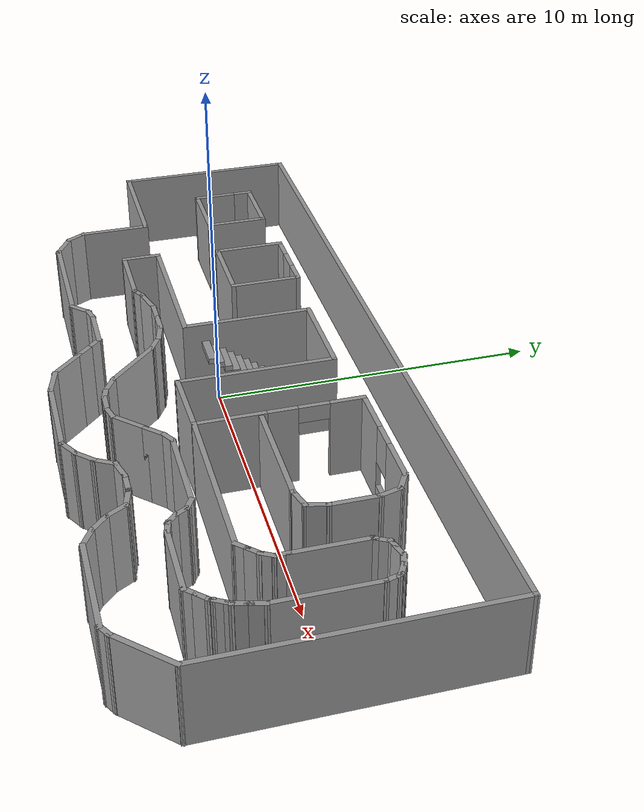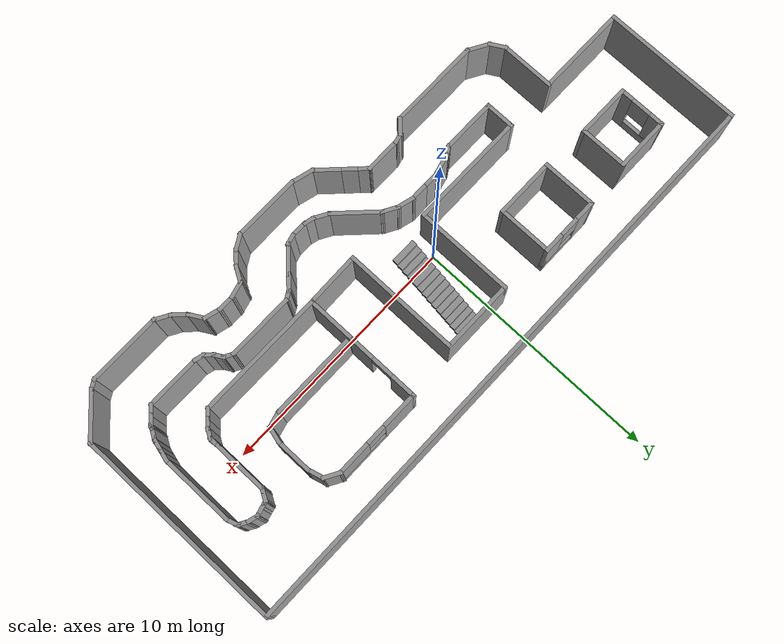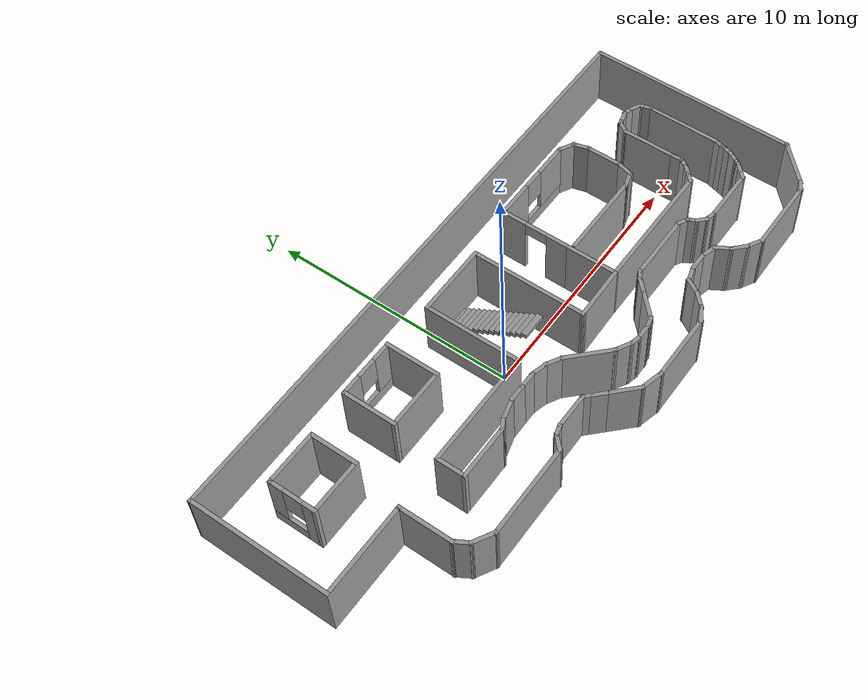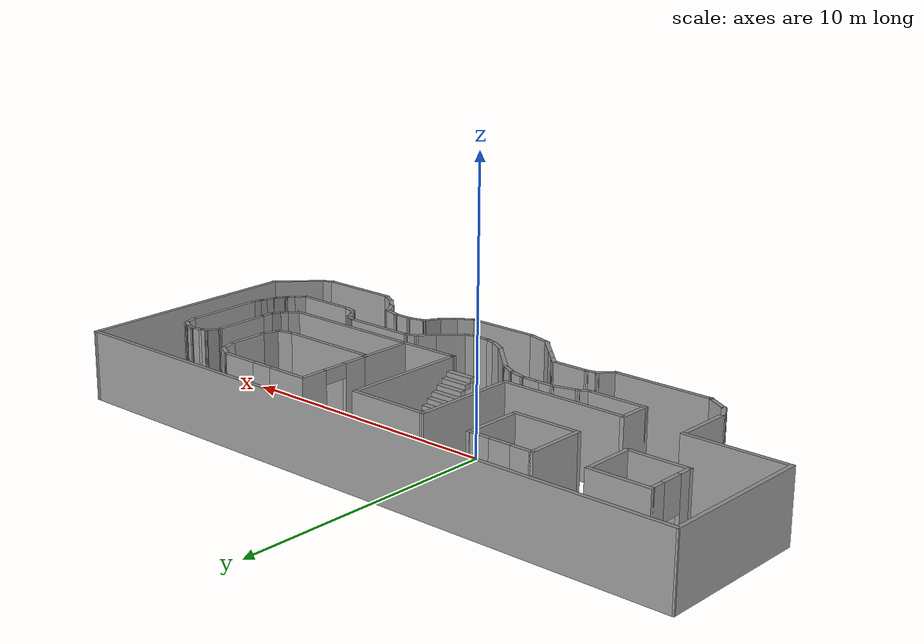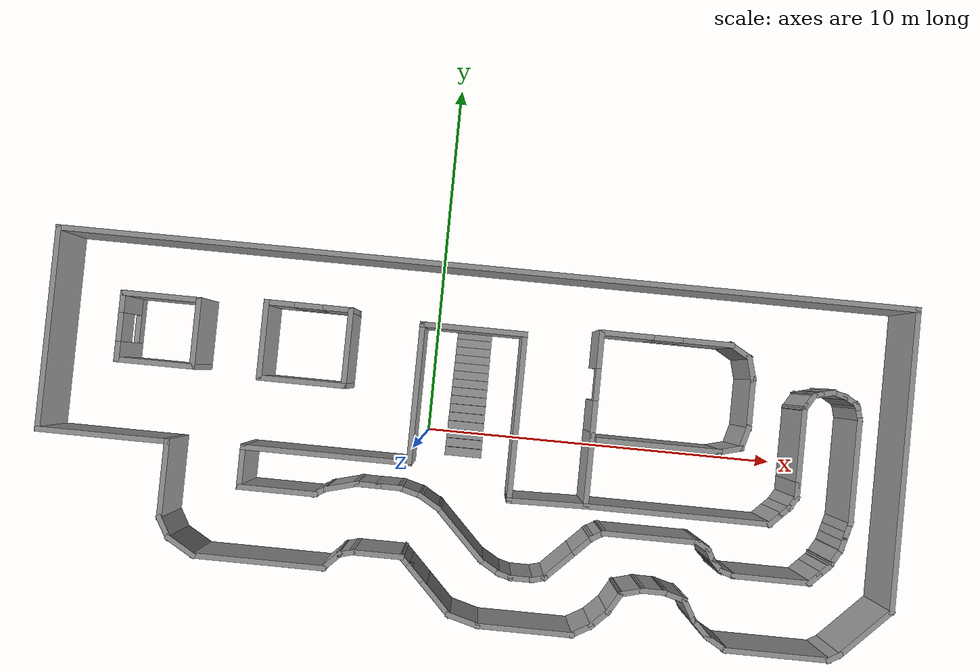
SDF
<?xml version='1.0'?>
<sdf version='1.7'>
  <model name='parcial_este_sii'>
    <pose>1.2832 -0.231354 0 0 -0 0</pose>
    <link name='Stairs_0'>
      <visual name='Stairs_0_Visual_0'>
        <pose>-0.212158 3.06479 0.083333 0 -0 0</pose>
        <geometry>
          <box>
            <size>1 0.233333 0.166667</size>
          </box>
        </geometry>
        <material>
          <script>
            <uri>file://media/materials/scripts/gazebo.material</uri>
            <name>Gazebo/Grey</name>
          </script>
          <ambient>1 1 1 1</ambient>
        </material>
        <meta>
          <layer>0</layer>
        </meta>
      </visual>
      <collision name='Stairs_0_Collision_0'>
        <geometry>
          <box>
            <size>1 0.233333 0.166667</size>
          </box>
        </geometry>
        <pose>-0.212158 3.06479 0.083333 0 -0 0</pose>
      </collision>
      <visual name='Stairs_0_Visual_1'>
        <pose>-0.212158 2.83145 0.25 0 -0 0</pose>
        <geometry>
          <box>
            <size>1 0.233333 0.166667</size>
          </box>
        </geometry>
        <material>
          <script>
            <uri>file://media/materials/scripts/gazebo.material</uri>
            <name>Gazebo/Grey</name>
          </script>
          <ambient>1 1 1 1</ambient>
        </material>
        <meta>
          <layer>0</layer>
        </meta>
      </visual>
      <collision name='Stairs_0_Collision_1'>
        <geometry>
          <box>
            <size>1 0.233333 0.166667</size>
          </box>
        </geometry>
        <pose>-0.212158 2.83145 0.25 0 -0 0</pose>
      </collision>
      <visual name='Stairs_0_Visual_2'>
        <pose>-0.212158 2.59812 0.416667 0 -0 0</pose>
        <geometry>
          <box>
            <size>1 0.233333 0.166667</size>
          </box>
        </geometry>
        <material>
          <script>
            <uri>file://media/materials/scripts/gazebo.material</uri>
            <name>Gazebo/Grey</name>
          </script>
          <ambient>1 1 1 1</ambient>
        </material>
        <meta>
          <layer>0</layer>
        </meta>
      </visual>
      <collision name='Stairs_0_Collision_2'>
        <geometry>
          <box>
            <size>1 0.233333 0.166667</size>
          </box>
        </geometry>
        <pose>-0.212158 2.59812 0.416667 0 -0 0</pose>
      </collision>
      <visual name='Stairs_0_Visual_3'>
        <pose>-0.212158 2.36479 0.583333 0 -0 0</pose>
        <geometry>
          <box>
            <size>1 0.233333 0.166667</size>
          </box>
        </geometry>
        <material>
          <script>
            <uri>file://media/materials/scripts/gazebo.material</uri>
            <name>Gazebo/Grey</name>
          </script>
          <ambient>1 1 1 1</ambient>
        </material>
        <meta>
          <layer>0</layer>
        </meta>
      </visual>
      <collision name='Stairs_0_Collision_3'>
        <geometry>
          <box>
            <size>1 0.233333 0.166667</size>
          </box>
        </geometry>
        <pose>-0.212158 2.36479 0.583333 0 -0 0</pose>
      </collision>
      <visual name='Stairs_0_Visual_4'>
        <pose>-0.212158 2.13145 0.75 0 -0 0</pose>
        <geometry>
          <box>
            <size>1 0.233333 0.166667</size>
          </box>
        </geometry>
        <material>
          <script>
            <uri>file://media/materials/scripts/gazebo.material</uri>
            <name>Gazebo/Grey</name>
          </script>
          <ambient>1 1 1 1</ambient>
        </material>
        <meta>
          <layer>0</layer>
        </meta>
      </visual>
      <collision name='Stairs_0_Collision_4'>
        <geometry>
          <box>
            <size>1 0.233333 0.166667</size>
          </box>
        </geometry>
        <pose>-0.212158 2.13145 0.75 0 -0 0</pose>
      </collision>
      <visual name='Stairs_0_Visual_5'>
        <pose>-0.212158 1.89812 0.916667 0 -0 0</pose>
        <geometry>
          <box>
            <size>1 0.233333 0.166667</size>
          </box>
        </geometry>
        <material>
          <script>
            <uri>file://media/materials/scripts/gazebo.material</uri>
            <name>Gazebo/Grey</name>
          </script>
          <ambient>1 1 1 1</ambient>
        </material>
        <meta>
          <layer>0</layer>
        </meta>
      </visual>
      <collision name='Stairs_0_Collision_5'>
        <geometry>
          <box>
            <size>1 0.233333 0.166667</size>
          </box>
        </geometry>
        <pose>-0.212158 1.89812 0.916667 0 -0 0</pose>
      </collision>
      <visual name='Stairs_0_Visual_6'>
        <pose>-0.212158 1.66479 1.08333 0 -0 0</pose>
        <geometry>
          <box>
            <size>1 0.233333 0.166667</size>
          </box>
        </geometry>
        <material>
          <script>
            <uri>file://media/materials/scripts/gazebo.material</uri>
            <name>Gazebo/Grey</name>
          </script>
          <ambient>1 1 1 1</ambient>
        </material>
        <meta>
          <layer>0</layer>
        </meta>
      </visual>
      <collision name='Stairs_0_Collision_6'>
        <geometry>
          <box>
            <size>1 0.233333 0.166667</size>
          </box>
        </geometry>
        <pose>-0.212158 1.66479 1.08333 0 -0 0</pose>
      </collision>
      <visual name='Stairs_0_Visual_7'>
        <pose>-0.212158 1.43145 1.25 0 -0 0</pose>
        <geometry>
          <box>
            <size>1 0.233333 0.166667</size>
          </box>
        </geometry>
        <material>
          <script>
            <uri>file://media/materials/scripts/gazebo.material</uri>
            <name>Gazebo/Grey</name>
          </script>
          <ambient>1 1 1 1</ambient>
        </material>
        <meta>
          <layer>0</layer>
        </meta>
      </visual>
      <collision name='Stairs_0_Collision_7'>
        <geometry>
          <box>
            <size>1 0.233333 0.166667</size>
          </box>
        </geometry>
        <pose>-0.212158 1.43145 1.25 0 -0 0</pose>
      </collision>
      <visual name='Stairs_0_Visual_8'>
        <pose>-0.212158 1.19812 1.41667 0 -0 0</pose>
        <geometry>
          <box>
            <size>1 0.233333 0.166667</size>
          </box>
        </geometry>
        <material>
          <script>
            <uri>file://media/materials/scripts/gazebo.material</uri>
            <name>Gazebo/Grey</name>
          </script>
          <ambient>1 1 1 1</ambient>
        </material>
        <meta>
          <layer>0</layer>
        </meta>
      </visual>
      <collision name='Stairs_0_Collision_8'>
        <geometry>
          <box>
            <size>1 0.233333 0.166667</size>
          </box>
        </geometry>
        <pose>-0.212158 1.19812 1.41667 0 -0 0</pose>
      </collision>
      <visual name='Stairs_0_Visual_9'>
        <pose>-0.212158 0.964787 1.58333 0 -0 0</pose>
        <geometry>
          <box>
            <size>1 0.233333 0.166667</size>
          </box>
        </geometry>
        <material>
          <script>
            <uri>file://media/materials/scripts/gazebo.material</uri>
            <name>Gazebo/Grey</name>
          </script>
          <ambient>1 1 1 1</ambient>
        </material>
        <meta>
          <layer>0</layer>
        </meta>
      </visual>
      <collision name='Stairs_0_Collision_9'>
        <geometry>
          <box>
            <size>1 0.233333 0.166667</size>
          </box>
        </geometry>
        <pose>-0.212158 0.964787 1.58333 0 -0 0</pose>
      </collision>
      <visual name='Stairs_0_Visual_10'>
        <pose>-0.212158 0.731454 1.75 0 -0 0</pose>
        <geometry>
          <box>
            <size>1 0.233333 0.166667</size>
          </box>
        </geometry>
        <material>
          <script>
            <uri>file://media/materials/scripts/gazebo.material</uri>
            <name>Gazebo/Grey</name>
          </script>
          <ambient>1 1 1 1</ambient>
        </material>
        <meta>
          <layer>0</layer>
        </meta>
      </visual>
      <collision name='Stairs_0_Collision_10'>
        <geometry>
          <box>
            <size>1 0.233333 0.166667</size>
          </box>
        </geometry>
        <pose>-0.212158 0.731454 1.75 0 -0 0</pose>
      </collision>
      <visual name='Stairs_0_Visual_11'>
        <pose>-0.212158 0.49812 1.91667 0 -0 0</pose>
        <geometry>
          <box>
            <size>1 0.233333 0.166667</size>
          </box>
        </geometry>
        <material>
          <script>
            <uri>file://media/materials/scripts/gazebo.material</uri>
            <name>Gazebo/Grey</name>
          </script>
          <ambient>1 1 1 1</ambient>
        </material>
        <meta>
          <layer>0</layer>
        </meta>
      </visual>
      <collision name='Stairs_0_Collision_11'>
        <geometry>
          <box>
            <size>1 0.233333 0.166667</size>
          </box>
        </geometry>
        <pose>-0.212158 0.49812 1.91667 0 -0 0</pose>
      </collision>
      <visual name='Stairs_0_Visual_12'>
        <pose>-0.212158 0.264787 2.08333 0 -0 0</pose>
        <geometry>
          <box>
            <size>1 0.233333 0.166667</size>
          </box>
        </geometry>
        <material>
          <script>
            <uri>file://media/materials/scripts/gazebo.material</uri>
            <name>Gazebo/Grey</name>
          </script>
          <ambient>1 1 1 1</ambient>
        </material>
        <meta>
          <layer>0</layer>
        </meta>
      </visual>
      <collision name='Stairs_0_Collision_12'>
        <geometry>
          <box>
            <size>1 0.233333 0.166667</size>
          </box>
        </geometry>
        <pose>-0.212158 0.264787 2.08333 0 -0 0</pose>
      </collision>
      <visual name='Stairs_0_Visual_13'>
        <pose>-0.212158 0.031454 2.25 0 -0 0</pose>
        <geometry>
          <box>
            <size>1 0.233333 0.166667</size>
          </box>
        </geometry>
        <material>
          <script>
            <uri>file://media/materials/scripts/gazebo.material</uri>
            <name>Gazebo/Grey</name>
          </script>
          <ambient>1 1 1 1</ambient>
        </material>
        <meta>
          <layer>0</layer>
        </meta>
      </visual>
      <collision name='Stairs_0_Collision_13'>
        <geometry>
          <box>
            <size>1 0.233333 0.166667</size>
          </box>
        </geometry>
        <pose>-0.212158 0.031454 2.25 0 -0 0</pose>
      </collision>
      <visual name='Stairs_0_Visual_14'>
        <pose>-0.212158 -0.20188 2.41667 0 -0 0</pose>
        <geometry>
          <box>
            <size>1 0.233333 0.166667</size>
          </box>
        </geometry>
        <material>
          <script>
            <uri>file://media/materials/scripts/gazebo.material</uri>
            <name>Gazebo/Grey</name>
          </script>
          <ambient>1 1 1 1</ambient>
        </material>
        <meta>
          <layer>0</layer>
        </meta>
      </visual>
      <collision name='Stairs_0_Collision_14'>
        <geometry>
          <box>
            <size>1 0.233333 0.166667</size>
          </box>
        </geometry>
        <pose>-0.212158 -0.20188 2.41667 0 -0 0</pose>
      </collision>
    </link>
    <link name='Wall_100'>
      <collision name='Wall_100_Collision'>
        <geometry>
          <box>
            <size>0.75 0.15 2.5</size>
          </box>
        </geometry>
        <pose>0 0 1.25 0 -0 0</pose>
      </collision>
      <visual name='Wall_100_Visual'>
        <pose>0 0 1.25 0 -0 0</pose>
        <geometry>
          <box>
            <size>0.75 0.15 2.5</size>
          </box>
        </geometry>
        <material>
          <script>
            <uri>file://media/materials/scripts/gazebo.material</uri>
            <name>Gazebo/Grey</name>
          </script>
          <ambient>1 1 1 1</ambient>
        </material>
        <meta>
          <layer>0</layer>
        </meta>
      </visual>
      <pose>-1.171 -3.69295 0 0 -0 -0.785398</pose>
    </link>
    <link name='Wall_101'>
      <collision name='Wall_101_Collision'>
        <geometry>
          <box>
            <size>1.25 0.15 2.5</size>
          </box>
        </geometry>
        <pose>0 0 1.25 0 -0 0</pose>
      </collision>
      <visual name='Wall_101_Visual'>
        <pose>0 0 1.25 0 -0 0</pose>
        <geometry>
          <box>
            <size>1.25 0.15 2.5</size>
          </box>
        </geometry>
        <material>
          <script>
            <uri>file://media/materials/scripts/gazebo.material</uri>
            <name>Gazebo/Grey</name>
          </script>
          <ambient>1 1 1 1</ambient>
        </material>
        <meta>
          <layer>0</layer>
        </meta>
      </visual>
      <pose>-0.569956 -4.294 0 0 -0 -0.785398</pose>
    </link>
    <link name='Wall_102'>
      <collision name='Wall_102_Collision'>
        <geometry>
          <box>
            <size>1 0.15 2.5</size>
          </box>
        </geometry>
        <pose>0 0 1.25 0 -0 0</pose>
      </collision>
      <visual name='Wall_102_Visual'>
        <pose>0 0 1.25 0 -0 0</pose>
        <geometry>
          <box>
            <size>1 0.15 2.5</size>
          </box>
        </geometry>
        <material>
          <script>
            <uri>file://media/materials/scripts/gazebo.material</uri>
            <name>Gazebo/Grey</name>
          </script>
          <ambient>1 1 1 1</ambient>
        </material>
        <meta>
          <layer>0</layer>
        </meta>
      </visual>
      <pose>0.229471 -4.7929 0 0 -0 -0.261799</pose>
    </link>
    <link name='Wall_103'>
      <collision name='Wall_103_Collision'>
        <geometry>
          <box>
            <size>2.75 0.15 2.5</size>
          </box>
        </geometry>
        <pose>0 0 1.25 0 -0 0</pose>
      </collision>
      <visual name='Wall_103_Visual'>
        <pose>0 0 1.25 0 -0 0</pose>
        <geometry>
          <box>
            <size>2.75 0.15 2.5</size>
          </box>
        </geometry>
        <material>
          <script>
            <uri>file://media/materials/scripts/gazebo.material</uri>
            <name>Gazebo/Grey</name>
          </script>
          <ambient>1 1 1 1</ambient>
        </material>
        <meta>
          <layer>0</layer>
        </meta>
      </visual>
      <pose>1.93999 -4.9029 0 0 -0 0</pose>
    </link>
    <link name='Wall_104'>
      <collision name='Wall_104_Collision'>
        <geometry>
          <box>
            <size>0.75 0.15 2.5</size>
          </box>
        </geometry>
        <pose>0 0 1.25 0 -0 0</pose>
      </collision>
      <visual name='Wall_104_Visual'>
        <pose>0 0 1.25 0 -0 0</pose>
        <geometry>
          <box>
            <size>0.75 0.15 2.5</size>
          </box>
        </geometry>
        <material>
          <script>
            <uri>file://media/materials/scripts/gazebo.material</uri>
            <name>Gazebo/Grey</name>
          </script>
          <ambient>1 1 1 1</ambient>
        </material>
        <meta>
          <layer>0</layer>
        </meta>
      </visual>
      <pose>3.4998 -4.7529 0 0 -0 0.523599</pose>
    </link>
    <link name='Wall_105'>
      <collision name='Wall_105_Collision'>
        <geometry>
          <box>
            <size>0.75 0.15 2.5</size>
          </box>
        </geometry>
        <pose>0 0 1.25 0 -0 0</pose>
      </collision>
      <visual name='Wall_105_Visual'>
        <pose>0 0 1.25 0 -0 0</pose>
        <geometry>
          <box>
            <size>0.75 0.15 2.5</size>
          </box>
        </geometry>
        <material>
          <script>
            <uri>file://media/materials/scripts/gazebo.material</uri>
            <name>Gazebo/Grey</name>
          </script>
          <ambient>1 1 1 1</ambient>
        </material>
        <meta>
          <layer>0</layer>
        </meta>
      </visual>
      <pose>3.97174 -4.39077 0 0 -0 0.785398</pose>
    </link>
    <link name='Wall_106'>
      <collision name='Wall_106_Collision'>
        <geometry>
          <box>
            <size>0.75 0.15 2.5</size>
          </box>
        </geometry>
        <pose>0 0 1.25 0 -0 0</pose>
      </collision>
      <visual name='Wall_106_Visual'>
        <pose>0 0 1.25 0 -0 0</pose>
        <geometry>
          <box>
            <size>0.75 0.15 2.5</size>
          </box>
        </geometry>
        <material>
          <script>
            <uri>file://media/materials/scripts/gazebo.material</uri>
            <name>Gazebo/Grey</name>
          </script>
          <ambient>1 1 1 1</ambient>
        </material>
        <meta>
          <layer>0</layer>
        </meta>
      </visual>
      <pose>4.33387 -3.91883 0 0 -0 1.0472</pose>
    </link>
    <link name='Wall_107'>
      <collision name='Wall_107_Collision'>
        <geometry>
          <box>
            <size>0.75 0.15 2.5</size>
          </box>
        </geometry>
        <pose>0 0 1.25 0 -0 0</pose>
      </collision>
      <visual name='Wall_107_Visual'>
        <pose>0 0 1.25 0 -0 0</pose>
        <geometry>
          <box>
            <size>0.75 0.15 2.5</size>
          </box>
        </geometry>
        <material>
          <script>
            <uri>file://media/materials/scripts/gazebo.material</uri>
            <name>Gazebo/Grey</name>
          </script>
          <ambient>1 1 1 1</ambient>
        </material>
        <meta>
          <layer>0</layer>
        </meta>
      </visual>
      <pose>4.77365 -3.58138 0 0 -0 0.261799</pose>
    </link>
    <link name='Wall_108'>
      <collision name='Wall_108_Collision'>
        <geometry>
          <box>
            <size>0.75 0.15 2.5</size>
          </box>
        </geometry>
        <pose>0 0 1.25 0 -0 0</pose>
      </collision>
      <visual name='Wall_108_Visual'>
        <pose>0 0 1.25 0 -0 0</pose>
        <geometry>
          <box>
            <size>0.75 0.15 2.5</size>
          </box>
        </geometry>
        <material>
          <script>
            <uri>file://media/materials/scripts/gazebo.material</uri>
            <name>Gazebo/Grey</name>
          </script>
          <ambient>1 1 1 1</ambient>
        </material>
        <meta>
          <layer>0</layer>
        </meta>
      </visual>
      <pose>5.36342 -3.50373 0 0 -0 0</pose>
    </link>
    <link name='Wall_109'>
      <collision name='Wall_109_Collision'>
        <geometry>
          <box>
            <size>0.75 0.15 2.5</size>
          </box>
        </geometry>
        <pose>0 0 1.25 0 -0 0</pose>
      </collision>
      <visual name='Wall_109_Visual'>
        <pose>0 0 1.25 0 -0 0</pose>
        <geometry>
          <box>
            <size>0.75 0.15 2.5</size>
          </box>
        </geometry>
        <material>
          <script>
            <uri>file://media/materials/scripts/gazebo.material</uri>
            <name>Gazebo/Grey</name>
          </script>
          <ambient>1 1 1 1</ambient>
        </material>
        <meta>
          <layer>0</layer>
        </meta>
      </visual>
      <pose>5.9532 -3.58138 0 0 -0 -0.261799</pose>
    </link>
    <link name='Wall_11'>
      <collision name='Wall_11_Collision'>
        <geometry>
          <box>
            <size>2.10889 0.15 2.5</size>
          </box>
        </geometry>
        <pose>0 0 1.25 0 -0 0</pose>
      </collision>
      <visual name='Wall_11_Visual'>
        <pose>0 0 1.25 0 -0 0</pose>
        <geometry>
          <box>
            <size>2.10889 0.15 2.5</size>
          </box>
        </geometry>
        <material>
          <script>
            <uri>file://media/materials/scripts/gazebo.material</uri>
            <name>Gazebo/Grey</name>
          </script>
          <ambient>1 1 1 1</ambient>
        </material>
        <meta>
          <layer>0</layer>
        </meta>
      </visual>
      <pose>3.29186 -0.374165 0 0 -0 -1.5708</pose>
    </link>
    <link name='Wall_110'>
      <collision name='Wall_110_Collision'>
        <geometry>
          <box>
            <size>0.75 0.15 2.5</size>
          </box>
        </geometry>
        <pose>0 0 1.25 0 -0 0</pose>
      </collision>
      <visual name='Wall_110_Visual'>
        <pose>0 0 1.25 0 -0 0</pose>
        <geometry>
          <box>
            <size>0.75 0.15 2.5</size>
          </box>
        </geometry>
        <material>
          <script>
            <uri>file://media/materials/scripts/gazebo.material</uri>
            <name>Gazebo/Grey</name>
          </script>
          <ambient>1 1 1 1</ambient>
        </material>
        <meta>
          <layer>0</layer>
        </meta>
      </visual>
      <pose>6.39298 -3.91883 0 0 -0 -1.0472</pose>
    </link>
    <link name='Wall_111'>
      <collision name='Wall_111_Collision'>
        <geometry>
          <box>
            <size>0.75 0.15 2.5</size>
          </box>
        </geometry>
        <pose>0 0 1.25 0 -0 0</pose>
      </collision>
      <visual name='Wall_111_Visual'>
        <pose>0 0 1.25 0 -0 0</pose>
        <geometry>
          <box>
            <size>0.75 0.15 2.5</size>
          </box>
        </geometry>
        <material>
          <script>
            <uri>file://media/materials/scripts/gazebo.material</uri>
            <name>Gazebo/Grey</name>
          </script>
          <ambient>1 1 1 1</ambient>
        </material>
        <meta>
          <layer>0</layer>
        </meta>
      </visual>
      <pose>6.75511 -4.39077 0 0 -0 -0.785398</pose>
    </link>
    <link name='Wall_112'>
      <collision name='Wall_112_Collision'>
        <geometry>
          <box>
            <size>0.75 0.15 2.5</size>
          </box>
        </geometry>
        <pose>0 0 1.25 0 -0 0</pose>
      </collision>
      <visual name='Wall_112_Visual'>
        <pose>0 0 1.25 0 -0 0</pose>
        <geometry>
          <box>
            <size>0.75 0.15 2.5</size>
          </box>
        </geometry>
        <material>
          <script>
            <uri>file://media/materials/scripts/gazebo.material</uri>
            <name>Gazebo/Grey</name>
          </script>
          <ambient>1 1 1 1</ambient>
        </material>
        <meta>
          <layer>0</layer>
        </meta>
      </visual>
      <pose>7.22705 -4.7529 0 0 -0 -0.523599</pose>
    </link>
    <link name='Wall_113'>
      <collision name='Wall_113_Collision'>
        <geometry>
          <box>
            <size>3 0.15 2.5</size>
          </box>
        </geometry>
        <pose>0 0 1.25 0 -0 0</pose>
      </collision>
      <visual name='Wall_113_Visual'>
        <pose>0 0 1.25 0 -0 0</pose>
        <geometry>
          <box>
            <size>3 0.15 2.5</size>
          </box>
        </geometry>
        <material>
          <script>
            <uri>file://media/materials/scripts/gazebo.material</uri>
            <name>Gazebo/Grey</name>
          </script>
          <ambient>1 1 1 1</ambient>
        </material>
        <meta>
          <layer>0</layer>
        </meta>
      </visual>
      <pose>8.91186 -4.9029 0 0 -0 0</pose>
    </link>
    <link name='Wall_114'>
      <collision name='Wall_114_Collision'>
        <geometry>
          <box>
            <size>0.5 0.15 2.5</size>
          </box>
        </geometry>
        <pose>0 0 1.25 0 -0 0</pose>
      </collision>
      <visual name='Wall_114_Visual'>
        <pose>0 0 1.25 0 -0 0</pose>
        <geometry>
          <box>
            <size>0.5 0.15 2.5</size>
          </box>
        </geometry>
        <material>
          <script>
            <uri>file://media/materials/scripts/gazebo.material</uri>
            <name>Gazebo/Grey</name>
          </script>
          <ambient>1 1 1 1</ambient>
        </material>
        <meta>
          <layer>0</layer>
        </meta>
      </visual>
      <pose>10.4884 -4.8154 0 0 -0 0.523599</pose>
    </link>
    <link name='Wall_116'>
      <collision name='Wall_116_Collision'>
        <geometry>
          <box>
            <size>2 0.15 2.5</size>
          </box>
        </geometry>
        <pose>0 0 1.25 0 -0 0</pose>
      </collision>
      <visual name='Wall_116_Visual'>
        <pose>0 0 1.25 0 -0 0</pose>
        <geometry>
          <box>
            <size>2 0.15 2.5</size>
          </box>
        </geometry>
        <material>
          <script>
            <uri>file://media/materials/scripts/gazebo.material</uri>
            <name>Gazebo/Grey</name>
          </script>
          <ambient>1 1 1 1</ambient>
        </material>
        <meta>
          <layer>0</layer>
        </meta>
      </visual>
      <pose>11.294 -4.07383 0 0 -0 0.785398</pose>
    </link>
    <link name='Wall_117'>
      <collision name='Wall_117_Collision'>
        <geometry>
          <box>
            <size>8.5 0.15 2.5</size>
          </box>
        </geometry>
        <pose>0 0 1.25 0 -0 0</pose>
      </collision>
      <visual name='Wall_117_Visual'>
        <pose>0 0 1.25 0 -0 0</pose>
        <geometry>
          <box>
            <size>8.5 0.15 2.5</size>
          </box>
        </geometry>
        <material>
          <script>
            <uri>file://media/materials/scripts/gazebo.material</uri>
            <name>Gazebo/Grey</name>
          </script>
          <ambient>1 1 1 1</ambient>
        </material>
        <meta>
          <layer>0</layer>
        </meta>
      </visual>
      <pose>11.9481 0.755247 0 0 -0 1.5708</pose>
    </link>
    <link name='Wall_118'>
      <collision name='Wall_118_Collision'>
        <geometry>
          <box>
            <size>24.0772 0.15 2.5</size>
          </box>
        </geometry>
        <pose>0 0 1.25 0 -0 0</pose>
      </collision>
      <visual name='Wall_118_Visual'>
        <pose>0 0 1.25 0 -0 0</pose>
        <geometry>
          <box>
            <size>24.0772 0.15 2.5</size>
          </box>
        </geometry>
        <material>
          <script>
            <uri>file://media/materials/scripts/gazebo.material</uri>
            <name>Gazebo/Grey</name>
          </script>
          <ambient>1 1 1 1</ambient>
        </material>
        <meta>
          <layer>0</layer>
        </meta>
      </visual>
      <pose>-0.01548 4.91334 0 0 -0 -3.14018</pose>
    </link>
    <link name='Wall_12'>
      <collision name='Wall_12_Collision'>
        <geometry>
          <box>
            <size>5.25 0.15 2.5</size>
          </box>
        </geometry>
        <pose>0 0 1.25 0 -0 0</pose>
      </collision>
      <visual name='Wall_12_Visual'>
        <pose>0 0 1.25 0 -0 0</pose>
        <geometry>
          <box>
            <size>5.25 0.15 2.5</size>
          </box>
        </geometry>
        <material>
          <script>
            <uri>file://media/materials/scripts/gazebo.material</uri>
            <name>Gazebo/Grey</name>
          </script>
          <ambient>1 1 1 1</ambient>
        </material>
        <meta>
          <layer>0</layer>
        </meta>
      </visual>
      <pose>5.84186 -1.35361 0 0 -0 0</pose>
    </link>
    <link name='Wall_13'>
      <collision name='Wall_13_Collision'>
        <geometry>
          <box>
            <size>0.5 0.15 2.5</size>
          </box>
        </geometry>
        <pose>0 0 1.25 0 -0 0</pose>
      </collision>
      <visual name='Wall_13_Visual'>
        <pose>0 0 1.25 0 -0 0</pose>
        <geometry>
          <box>
            <size>0.5 0.15 2.5</size>
          </box>
        </geometry>
        <material>
          <script>
            <uri>file://media/materials/scripts/gazebo.material</uri>
            <name>Gazebo/Grey</name>
          </script>
          <ambient>1 1 1 1</ambient>
        </material>
        <meta>
          <layer>0</layer>
        </meta>
      </visual>
      <pose>8.5156 -1.22986 0 0 -0 0.785398</pose>
    </link>
    <link name='Wall_14'>
      <collision name='Wall_14_Collision'>
        <geometry>
          <box>
            <size>0.5 0.15 2.5</size>
          </box>
        </geometry>
        <pose>0 0 1.25 0 -0 0</pose>
      </collision>
      <visual name='Wall_14_Visual'>
        <pose>0 0 1.25 0 -0 0</pose>
        <geometry>
          <box>
            <size>0.5 0.15 2.5</size>
          </box>
        </geometry>
        <material>
          <script>
            <uri>file://media/materials/scripts/gazebo.material</uri>
            <name>Gazebo/Grey</name>
          </script>
          <ambient>1 1 1 1</ambient>
        </material>
        <meta>
          <layer>0</layer>
        </meta>
      </visual>
      <pose>8.76309 -0.982378 0 0 -0 0.785398</pose>
    </link>
    <link name='Wall_15'>
      <collision name='Wall_15_Collision'>
        <geometry>
          <box>
            <size>0.5 0.15 2.5</size>
          </box>
        </geometry>
        <pose>0 0 1.25 0 -0 0</pose>
      </collision>
      <visual name='Wall_15_Visual'>
        <pose>0 0 1.25 0 -0 0</pose>
        <geometry>
          <box>
            <size>0.5 0.15 2.5</size>
          </box>
        </geometry>
        <material>
          <script>
            <uri>file://media/materials/scripts/gazebo.material</uri>
            <name>Gazebo/Grey</name>
          </script>
          <ambient>1 1 1 1</ambient>
        </material>
        <meta>
          <layer>0</layer>
        </meta>
      </visual>
      <pose>8.97433 -0.707079 0 0 -0 1.0472</pose>
    </link>
    <link name='Wall_16'>
      <collision name='Wall_16_Collision'>
        <geometry>
          <box>
            <size>0.5 0.15 2.5</size>
          </box>
        </geometry>
        <pose>0 0 1.25 0 -0 0</pose>
      </collision>
      <visual name='Wall_16_Visual'>
        <pose>0 0 1.25 0 -0 0</pose>
        <geometry>
          <box>
            <size>0.5 0.15 2.5</size>
          </box>
        </geometry>
        <material>
          <script>
            <uri>file://media/materials/scripts/gazebo.material</uri>
            <name>Gazebo/Grey</name>
          </script>
          <ambient>1 1 1 1</ambient>
        </material>
        <meta>
          <layer>0</layer>
        </meta>
      </visual>
      <pose>9.06184 -0.380525 0 0 -0 1.5708</pose>
    </link>
    <link name='Wall_17'>
      <collision name='Wall_17_Collision'>
        <geometry>
          <box>
            <size>2.25 0.15 2.5</size>
          </box>
        </geometry>
        <pose>0 0 1.25 0 -0 0</pose>
      </collision>
      <visual name='Wall_17_Visual'>
        <pose>0 0 1.25 0 -0 0</pose>
        <geometry>
          <box>
            <size>2.25 0.15 2.5</size>
          </box>
        </geometry>
        <material>
          <script>
            <uri>file://media/materials/scripts/gazebo.material</uri>
            <name>Gazebo/Grey</name>
          </script>
          <ambient>1 1 1 1</ambient>
        </material>
        <meta>
          <layer>0</layer>
        </meta>
      </visual>
      <pose>9.06184 0.844475 0 0 -0 1.5708</pose>
    </link>
    <link name='Wall_18'>
      <collision name='Wall_18_Collision'>
        <geometry>
          <box>
            <size>0.25 0.15 2.5</size>
          </box>
        </geometry>
        <pose>0 0 1.25 0 -0 0</pose>
      </collision>
      <visual name='Wall_18_Visual'>
        <pose>0 0 1.25 0 -0 0</pose>
        <geometry>
          <box>
            <size>0.25 0.15 2.5</size>
          </box>
        </geometry>
        <material>
          <script>
            <uri>file://media/materials/scripts/gazebo.material</uri>
            <name>Gazebo/Grey</name>
          </script>
          <ambient>1 1 1 1</ambient>
        </material>
        <meta>
          <layer>0</layer>
        </meta>
      </visual>
      <pose>9.08684 1.93778 0 0 -0 1.0472</pose>
    </link>
    <link name='Wall_19'>
      <collision name='Wall_19_Collision'>
        <geometry>
          <box>
            <size>0.5 0.15 2.5</size>
          </box>
        </geometry>
        <pose>0 0 1.25 0 -0 0</pose>
      </collision>
      <visual name='Wall_19_Visual'>
        <pose>0 0 1.25 0 -0 0</pose>
        <geometry>
          <box>
            <size>0.5 0.15 2.5</size>
          </box>
        </geometry>
        <material>
          <script>
            <uri>file://media/materials/scripts/gazebo.material</uri>
            <name>Gazebo/Grey</name>
          </script>
          <ambient>1 1 1 1</ambient>
        </material>
        <meta>
          <layer>0</layer>
        </meta>
      </visual>
      <pose>9.19933 2.13263 0 0 -0 1.0472</pose>
    </link>
    <link name='Wall_20'>
      <collision name='Wall_20_Collision'>
        <geometry>
          <box>
            <size>0.25 0.15 2.5</size>
          </box>
        </geometry>
        <pose>0 0 1.25 0 -0 0</pose>
      </collision>
      <visual name='Wall_20_Visual'>
        <pose>0 0 1.25 0 -0 0</pose>
        <geometry>
          <box>
            <size>0.25 0.15 2.5</size>
          </box>
        </geometry>
        <material>
          <script>
            <uri>file://media/materials/scripts/gazebo.material</uri>
            <name>Gazebo/Grey</name>
          </script>
          <ambient>1 1 1 1</ambient>
        </material>
        <meta>
          <layer>0</layer>
        </meta>
      </visual>
      <pose>9.33513 2.29713 0 0 -0 0.261799</pose>
    </link>
    <link name='Wall_21'>
      <collision name='Wall_21_Collision'>
        <geometry>
          <box>
            <size>0.25 0.15 2.5</size>
          </box>
        </geometry>
        <pose>0 0 1.25 0 -0 0</pose>
      </collision>
      <visual name='Wall_21_Visual'>
        <pose>0 0 1.25 0 -0 0</pose>
        <geometry>
          <box>
            <size>0.25 0.15 2.5</size>
          </box>
        </geometry>
        <material>
          <script>
            <uri>file://media/materials/scripts/gazebo.material</uri>
            <name>Gazebo/Grey</name>
          </script>
          <ambient>1 1 1 1</ambient>
        </material>
        <meta>
          <layer>0</layer>
        </meta>
      </visual>
      <pose>9.43172 2.32301 0 0 -0 0.261799</pose>
    </link>
    <link name='Wall_22'>
      <collision name='Wall_22_Collision'>
        <geometry>
          <box>
            <size>0.5 0.15 2.5</size>
          </box>
        </geometry>
        <pose>0 0 1.25 0 -0 0</pose>
      </collision>
      <visual name='Wall_22_Visual'>
        <pose>0 0 1.25 0 -0 0</pose>
        <geometry>
          <box>
            <size>0.5 0.15 2.5</size>
          </box>
        </geometry>
        <material>
          <script>
            <uri>file://media/materials/scripts/gazebo.material</uri>
            <name>Gazebo/Grey</name>
          </script>
          <ambient>1 1 1 1</ambient>
        </material>
        <meta>
          <layer>0</layer>
        </meta>
      </visual>
      <pose>9.64906 2.38124 0 0 -0 0.261799</pose>
    </link>
    <link name='Wall_23'>
      <collision name='Wall_23_Collision'>
        <geometry>
          <box>
            <size>0.5 0.15 2.5</size>
          </box>
        </geometry>
        <pose>0 0 1.25 0 -0 0</pose>
      </collision>
      <visual name='Wall_23_Visual'>
        <pose>0 0 1.25 0 -0 0</pose>
        <geometry>
          <box>
            <size>0.5 0.15 2.5</size>
          </box>
        </geometry>
        <material>
          <script>
            <uri>file://media/materials/scripts/gazebo.material</uri>
            <name>Gazebo/Grey</name>
          </script>
          <ambient>1 1 1 1</ambient>
        </material>
        <meta>
          <layer>0</layer>
        </meta>
      </visual>
      <pose>9.98713 2.38124 0 0 -0 -0.261799</pose>
    </link>
    <link name='Wall_24'>
      <collision name='Wall_24_Collision'>
        <geometry>
          <box>
            <size>0.5 0.15 2.5</size>
          </box>
        </geometry>
        <pose>0 0 1.25 0 -0 0</pose>
      </collision>
      <visual name='Wall_24_Visual'>
        <pose>0 0 1.25 0 -0 0</pose>
        <geometry>
          <box>
            <size>0.5 0.15 2.5</size>
          </box>
        </geometry>
        <material>
          <script>
            <uri>file://media/materials/scripts/gazebo.material</uri>
            <name>Gazebo/Grey</name>
          </script>
          <ambient>1 1 1 1</ambient>
        </material>
        <meta>
          <layer>0</layer>
        </meta>
      </visual>
      <pose>10.3077 2.24845 0 0 -0 -0.523599</pose>
    </link>
    <link name='Wall_25'>
      <collision name='Wall_25_Collision'>
        <geometry>
          <box>
            <size>0.25 0.15 2.5</size>
          </box>
        </geometry>
        <pose>0 0 1.25 0 -0 0</pose>
      </collision>
      <visual name='Wall_25_Visual'>
        <pose>0 0 1.25 0 -0 0</pose>
        <geometry>
          <box>
            <size>0.25 0.15 2.5</size>
          </box>
        </geometry>
        <material>
          <script>
            <uri>file://media/materials/scripts/gazebo.material</uri>
            <name>Gazebo/Grey</name>
          </script>
          <ambient>1 1 1 1</ambient>
        </material>
        <meta>
          <layer>0</layer>
        </meta>
      </visual>
      <pose>10.4843 2.11765 0 0 -0 -1.0472</pose>
    </link>
    <link name='Wall_26'>
      <collision name='Wall_26_Collision'>
        <geometry>
          <box>
            <size>0.5 0.15 2.5</size>
          </box>
        </geometry>
        <pose>0 0 1.25 0 -0 0</pose>
      </collision>
      <visual name='Wall_26_Visual'>
        <pose>0 0 1.25 0 -0 0</pose>
        <geometry>
          <box>
            <size>0.5 0.15 2.5</size>
          </box>
        </geometry>
        <material>
          <script>
            <uri>file://media/materials/scripts/gazebo.material</uri>
            <name>Gazebo/Grey</name>
          </script>
          <ambient>1 1 1 1</ambient>
        </material>
        <meta>
          <layer>0</layer>
        </meta>
      </visual>
      <pose>10.5546 1.90531 0 0 -0 -1.309</pose>
    </link>
    <link name='Wall_27'>
      <collision name='Wall_27_Collision'>
        <geometry>
          <box>
            <size>3 0.15 2.5</size>
          </box>
        </geometry>
        <pose>0 0 1.25 0 -0 0</pose>
      </collision>
      <visual name='Wall_27_Visual'>
        <pose>0 0 1.25 0 -0 0</pose>
        <geometry>
          <box>
            <size>3 0.15 2.5</size>
          </box>
        </geometry>
        <material>
          <script>
            <uri>file://media/materials/scripts/gazebo.material</uri>
            <name>Gazebo/Grey</name>
          </script>
          <ambient>1 1 1 1</ambient>
        </material>
        <meta>
          <layer>0</layer>
        </meta>
      </visual>
      <pose>10.5999 0.311274 0 0 -0 -1.5708</pose>
    </link>
    <link name='Wall_28'>
      <collision name='Wall_28_Collision'>
        <geometry>
          <box>
            <size>0.5 0.15 2.5</size>
          </box>
        </geometry>
        <pose>0 0 1.25 0 -0 0</pose>
      </collision>
      <visual name='Wall_28_Visual'>
        <pose>0 0 1.25 0 -0 0</pose>
        <geometry>
          <box>
            <size>0.5 0.15 2.5</size>
          </box>
        </geometry>
        <material>
          <script>
            <uri>file://media/materials/scripts/gazebo.material</uri>
            <name>Gazebo/Grey</name>
          </script>
          <ambient>1 1 1 1</ambient>
        </material>
        <meta>
          <layer>0</layer>
        </meta>
      </visual>
      <pose>10.5546 -1.28276 0 0 -0 -1.8326</pose>
    </link>
    <link name='Wall_29'>
      <collision name='Wall_29_Collision'>
        <geometry>
          <box>
            <size>0.25 0.15 2.5</size>
          </box>
        </geometry>
        <pose>0 0 1.25 0 -0 0</pose>
      </collision>
      <visual name='Wall_29_Visual'>
        <pose>0 0 1.25 0 -0 0</pose>
        <geometry>
          <box>
            <size>0.25 0.15 2.5</size>
          </box>
        </geometry>
        <material>
          <script>
            <uri>file://media/materials/scripts/gazebo.material</uri>
            <name>Gazebo/Grey</name>
          </script>
          <ambient>1 1 1 1</ambient>
        </material>
        <meta>
          <layer>0</layer>
        </meta>
      </visual>
      <pose>10.4963 -1.5001 0 0 -0 -1.8326</pose>
    </link>
    <link name='Wall_30'>
      <collision name='Wall_30_Collision'>
        <geometry>
          <box>
            <size>0.5 0.15 2.5</size>
          </box>
        </geometry>
        <pose>0 0 1.25 0 -0 0</pose>
      </collision>
      <visual name='Wall_30_Visual'>
        <pose>0 0 1.25 0 -0 0</pose>
        <geometry>
          <box>
            <size>0.5 0.15 2.5</size>
          </box>
        </geometry>
        <material>
          <script>
            <uri>file://media/materials/scripts/gazebo.material</uri>
            <name>Gazebo/Grey</name>
          </script>
          <ambient>1 1 1 1</ambient>
        </material>
        <meta>
          <layer>0</layer>
        </meta>
      </visual>
      <pose>10.4381 -1.71743 0 0 -0 -1.8326</pose>
    </link>
    <link name='Wall_31'>
      <collision name='Wall_31_Collision'>
        <geometry>
          <box>
            <size>0.25 0.15 2.5</size>
          </box>
        </geometry>
        <pose>0 0 1.25 0 -0 0</pose>
      </collision>
      <visual name='Wall_31_Visual'>
        <pose>0 0 1.25 0 -0 0</pose>
        <geometry>
          <box>
            <size>0.25 0.15 2.5</size>
          </box>
        </geometry>
        <material>
          <script>
            <uri>file://media/materials/scripts/gazebo.material</uri>
            <name>Gazebo/Grey</name>
          </script>
          <ambient>1 1 1 1</ambient>
        </material>
        <meta>
          <layer>0</layer>
        </meta>
      </visual>
      <pose>10.3678 -1.92977 0 0 -0 -2.0944</pose>
    </link>
    <link name='Wall_32'>
      <collision name='Wall_32_Collision'>
        <geometry>
          <box>
            <size>0.5 0.15 2.5</size>
          </box>
        </geometry>
        <pose>0 0 1.25 0 -0 0</pose>
      </collision>
      <visual name='Wall_32_Visual'>
        <pose>0 0 1.25 0 -0 0</pose>
        <geometry>
          <box>
            <size>0.5 0.15 2.5</size>
          </box>
        </geometry>
        <material>
          <script>
            <uri>file://media/materials/scripts/gazebo.material</uri>
            <name>Gazebo/Grey</name>
          </script>
          <ambient>1 1 1 1</ambient>
        </material>
        <meta>
          <layer>0</layer>
        </meta>
      </visual>
      <pose>10.2553 -2.12462 0 0 -0 -2.0944</pose>
    </link>
    <link name='Wall_33'>
      <collision name='Wall_33_Collision'>
        <geometry>
          <box>
            <size>0.15 0.15 2.5</size>
          </box>
        </geometry>
        <pose>0 0 1.25 0 -0 0</pose>
      </collision>
      <visual name='Wall_33_Visual'>
        <pose>0 0 1.25 0 -0 0</pose>
        <geometry>
          <box>
            <size>0.15 0.15 2.5</size>
          </box>
        </geometry>
        <material>
          <script>
            <uri>file://media/materials/scripts/gazebo.material</uri>
            <name>Gazebo/Grey</name>
          </script>
          <ambient>1 1 1 1</ambient>
        </material>
        <meta>
          <layer>0</layer>
        </meta>
      </visual>
      <pose>10.1678 -2.27618 0 0 -0 0</pose>
    </link>
    <link name='Wall_34'>
      <collision name='Wall_34_Collision'>
        <geometry>
          <box>
            <size>0.25 0.15 2.5</size>
          </box>
        </geometry>
        <pose>0 0 1.25 0 -0 0</pose>
      </collision>
      <visual name='Wall_34_Visual'>
        <pose>0 0 1.25 0 -0 0</pose>
        <geometry>
          <box>
            <size>0.25 0.15 2.5</size>
          </box>
        </geometry>
        <material>
          <script>
            <uri>file://media/materials/scripts/gazebo.material</uri>
            <name>Gazebo/Grey</name>
          </script>
          <ambient>1 1 1 1</ambient>
        </material>
        <meta>
          <layer>0</layer>
        </meta>
      </visual>
      <pose>10.1428 -2.31948 0 0 -0 -2.0944</pose>
    </link>
    <link name='Wall_35'>
      <collision name='Wall_35_Collision'>
        <geometry>
          <box>
            <size>0.5 0.15 2.5</size>
          </box>
        </geometry>
        <pose>0 0 1.25 0 -0 0</pose>
      </collision>
      <visual name='Wall_35_Visual'>
        <pose>0 0 1.25 0 -0 0</pose>
        <geometry>
          <box>
            <size>0.5 0.15 2.5</size>
          </box>
        </geometry>
        <material>
          <script>
            <uri>file://media/materials/scripts/gazebo.material</uri>
            <name>Gazebo/Grey</name>
          </script>
          <ambient>1 1 1 1</ambient>
        </material>
        <meta>
          <layer>0</layer>
        </meta>
      </visual>
      <pose>9.99407 -2.48652 0 0 -0 -2.35619</pose>
    </link>
    <link name='Wall_36'>
      <collision name='Wall_36_Collision'>
        <geometry>
          <box>
            <size>0.5 0.15 2.5</size>
          </box>
        </geometry>
        <pose>0 0 1.25 0 -0 0</pose>
      </collision>
      <visual name='Wall_36_Visual'>
        <pose>0 0 1.25 0 -0 0</pose>
        <geometry>
          <box>
            <size>0.5 0.15 2.5</size>
          </box>
        </geometry>
        <material>
          <script>
            <uri>file://media/materials/scripts/gazebo.material</uri>
            <name>Gazebo/Grey</name>
          </script>
          <ambient>1 1 1 1</ambient>
        </material>
        <meta>
          <layer>0</layer>
        </meta>
      </visual>
      <pose>9.74658 -2.73401 0 0 -0 -2.35619</pose>
    </link>
    <link name='Wall_37'>
      <collision name='Wall_37_Collision'>
        <geometry>
          <box>
            <size>2.25 0.15 2.5</size>
          </box>
        </geometry>
        <pose>0 0 1.25 0 -0 0</pose>
      </collision>
      <visual name='Wall_37_Visual'>
        <pose>0 0 1.25 0 -0 0</pose>
        <geometry>
          <box>
            <size>2.25 0.15 2.5</size>
          </box>
        </geometry>
        <material>
          <script>
            <uri>file://media/materials/scripts/gazebo.material</uri>
            <name>Gazebo/Grey</name>
          </script>
          <ambient>1 1 1 1</ambient>
        </material>
        <meta>
          <layer>0</layer>
        </meta>
      </visual>
      <pose>8.57283 -2.85776 0 0 -0 3.14159</pose>
    </link>
    <link name='Wall_38'>
      <collision name='Wall_38_Collision'>
        <geometry>
          <box>
            <size>0.5 0.15 2.5</size>
          </box>
        </geometry>
        <pose>0 0 1.25 0 -0 0</pose>
      </collision>
      <visual name='Wall_38_Visual'>
        <pose>0 0 1.25 0 -0 0</pose>
        <geometry>
          <box>
            <size>0.5 0.15 2.5</size>
          </box>
        </geometry>
        <material>
          <script>
            <uri>file://media/materials/scripts/gazebo.material</uri>
            <name>Gazebo/Grey</name>
          </script>
          <ambient>1 1 1 1</ambient>
        </material>
        <meta>
          <layer>0</layer>
        </meta>
      </visual>
      <pose>7.3538 -2.81246 0 0 -0 2.87979</pose>
    </link>
    <link name='Wall_39'>
      <collision name='Wall_39_Collision'>
        <geometry>
          <box>
            <size>0.5 0.15 2.5</size>
          </box>
        </geometry>
        <pose>0 0 1.25 0 -0 0</pose>
      </collision>
      <visual name='Wall_39_Visual'>
        <pose>0 0 1.25 0 -0 0</pose>
        <geometry>
          <box>
            <size>0.5 0.15 2.5</size>
          </box>
        </geometry>
        <material>
          <script>
            <uri>file://media/materials/scripts/gazebo.material</uri>
            <name>Gazebo/Grey</name>
          </script>
          <ambient>1 1 1 1</ambient>
        </material>
        <meta>
          <layer>0</layer>
        </meta>
      </visual>
      <pose>7.06102 -2.64343 0 0 -0 2.35619</pose>
    </link>
    <link name='Wall_40'>
      <collision name='Wall_40_Collision'>
        <geometry>
          <box>
            <size>0.5 0.15 2.5</size>
          </box>
        </geometry>
        <pose>0 0 1.25 0 -0 0</pose>
      </collision>
      <visual name='Wall_40_Visual'>
        <pose>0 0 1.25 0 -0 0</pose>
        <geometry>
          <box>
            <size>0.5 0.15 2.5</size>
          </box>
        </geometry>
        <material>
          <script>
            <uri>file://media/materials/scripts/gazebo.material</uri>
            <name>Gazebo/Grey</name>
          </script>
          <ambient>1 1 1 1</ambient>
        </material>
        <meta>
          <layer>0</layer>
        </meta>
      </visual>
      <pose>6.84977 -2.36813 0 0 -0 2.0944</pose>
    </link>
    <link name='Wall_41'>
      <collision name='Wall_41_Collision'>
        <geometry>
          <box>
            <size>0.5 0.15 2.5</size>
          </box>
        </geometry>
        <pose>0 0 1.25 0 -0 0</pose>
      </collision>
      <visual name='Wall_41_Visual'>
        <pose>0 0 1.25 0 -0 0</pose>
        <geometry>
          <box>
            <size>0.5 0.15 2.5</size>
          </box>
        </geometry>
        <material>
          <script>
            <uri>file://media/materials/scripts/gazebo.material</uri>
            <name>Gazebo/Grey</name>
          </script>
          <ambient>1 1 1 1</ambient>
        </material>
        <meta>
          <layer>0</layer>
        </meta>
      </visual>
      <pose>6.61072 -2.12907 0 0 -0 2.61799</pose>
    </link>
    <link name='Wall_42'>
      <collision name='Wall_42_Collision'>
        <geometry>
          <box>
            <size>2.75 0.15 2.5</size>
          </box>
        </geometry>
        <pose>0 0 1.25 0 -0 0</pose>
      </collision>
      <visual name='Wall_42_Visual'>
        <pose>0 0 1.25 0 -0 0</pose>
        <geometry>
          <box>
            <size>2.75 0.15 2.5</size>
          </box>
        </geometry>
        <material>
          <script>
            <uri>file://media/materials/scripts/gazebo.material</uri>
            <name>Gazebo/Grey</name>
          </script>
          <ambient>1 1 1 1</ambient>
        </material>
        <meta>
          <layer>0</layer>
        </meta>
      </visual>
      <pose>5.15916 -2.04157 0 0 -0 3.14159</pose>
    </link>
    <link name='Wall_43'>
      <collision name='Wall_43_Collision'>
        <geometry>
          <box>
            <size>0.5 0.15 2.5</size>
          </box>
        </geometry>
        <pose>0 0 1.25 0 -0 0</pose>
      </collision>
      <visual name='Wall_43_Visual'>
        <pose>0 0 1.25 0 -0 0</pose>
        <geometry>
          <box>
            <size>0.5 0.15 2.5</size>
          </box>
        </geometry>
        <material>
          <script>
            <uri>file://media/materials/scripts/gazebo.material</uri>
            <name>Gazebo/Grey</name>
          </script>
          <ambient>1 1 1 1</ambient>
        </material>
        <meta>
          <layer>0</layer>
        </meta>
      </visual>
      <pose>3.70761 -2.12907 0 0 -0 -2.61799</pose>
    </link>
    <link name='Wall_44'>
      <collision name='Wall_44_Collision'>
        <geometry>
          <box>
            <size>0.75 0.15 2.5</size>
          </box>
        </geometry>
        <pose>0 0 1.25 0 -0 0</pose>
      </collision>
      <visual name='Wall_44_Visual'>
        <pose>0 0 1.25 0 -0 0</pose>
        <geometry>
          <box>
            <size>0.75 0.15 2.5</size>
          </box>
        </geometry>
        <material>
          <script>
            <uri>file://media/materials/scripts/gazebo.material</uri>
            <name>Gazebo/Grey</name>
          </script>
          <ambient>1 1 1 1</ambient>
        </material>
        <meta>
          <layer>0</layer>
        </meta>
      </visual>
      <pose>3.34392 -2.4287 0 0 -0 -2.35619</pose>
    </link>
    <link name='Wall_47'>
      <collision name='Wall_47_Collision'>
        <geometry>
          <box>
            <size>1.25 0.15 2.5</size>
          </box>
        </geometry>
        <pose>0 0 1.25 0 -0 0</pose>
      </collision>
      <visual name='Wall_47_Visual'>
        <pose>0 0 1.25 0 -0 0</pose>
        <geometry>
          <box>
            <size>1.25 0.15 2.5</size>
          </box>
        </geometry>
        <material>
          <script>
            <uri>file://media/materials/scripts/gazebo.material</uri>
            <name>Gazebo/Grey</name>
          </script>
          <ambient>1 1 1 1</ambient>
        </material>
        <meta>
          <layer>0</layer>
        </meta>
      </visual>
      <pose>2.74288 -3.02975 0 0 -0 -2.35619</pose>
    </link>
    <link name='Wall_48'>
      <collision name='Wall_48_Collision'>
        <geometry>
          <box>
            <size>0.5 0.15 2.5</size>
          </box>
        </geometry>
        <pose>0 0 1.25 0 -0 0</pose>
      </collision>
      <visual name='Wall_48_Visual'>
        <pose>0 0 1.25 0 -0 0</pose>
        <geometry>
          <box>
            <size>0.5 0.15 2.5</size>
          </box>
        </geometry>
        <material>
          <script>
            <uri>file://media/materials/scripts/gazebo.material</uri>
            <name>Gazebo/Grey</name>
          </script>
          <ambient>1 1 1 1</ambient>
        </material>
        <meta>
          <layer>0</layer>
        </meta>
      </visual>
      <pose>2.18494 -3.46395 0 0 -0 -2.87979</pose>
    </link>
    <link name='Wall_49'>
      <collision name='Wall_49_Collision'>
        <geometry>
          <box>
            <size>0.75 0.15 2.5</size>
          </box>
        </geometry>
        <pose>0 0 1.25 0 -0 0</pose>
      </collision>
      <visual name='Wall_49_Visual'>
        <pose>0 0 1.25 0 -0 0</pose>
        <geometry>
          <box>
            <size>0.75 0.15 2.5</size>
          </box>
        </geometry>
        <material>
          <script>
            <uri>file://media/materials/scripts/gazebo.material</uri>
            <name>Gazebo/Grey</name>
          </script>
          <ambient>1 1 1 1</ambient>
        </material>
        <meta>
          <layer>0</layer>
        </meta>
      </visual>
      <pose>1.7159 -3.50924 0 0 -0 3.14159</pose>
    </link>
    <link name='Wall_50'>
      <collision name='Wall_50_Collision'>
        <geometry>
          <box>
            <size>0.5 0.15 2.5</size>
          </box>
        </geometry>
        <pose>0 0 1.25 0 -0 0</pose>
      </collision>
      <visual name='Wall_50_Visual'>
        <pose>0 0 1.25 0 -0 0</pose>
        <geometry>
          <box>
            <size>0.5 0.15 2.5</size>
          </box>
        </geometry>
        <material>
          <script>
            <uri>file://media/materials/scripts/gazebo.material</uri>
            <name>Gazebo/Grey</name>
          </script>
          <ambient>1 1 1 1</ambient>
        </material>
        <meta>
          <layer>0</layer>
        </meta>
      </visual>
      <pose>1.24686 -3.46395 0 0 -0 2.87979</pose>
    </link>
    <link name='Wall_51'>
      <collision name='Wall_51_Collision'>
        <geometry>
          <box>
            <size>0.75 0.15 2.5</size>
          </box>
        </geometry>
        <pose>0 0 1.25 0 -0 0</pose>
      </collision>
      <visual name='Wall_51_Visual'>
        <pose>0 0 1.25 0 -0 0</pose>
        <geometry>
          <box>
            <size>0.75 0.15 2.5</size>
          </box>
        </geometry>
        <material>
          <script>
            <uri>file://media/materials/scripts/gazebo.material</uri>
            <name>Gazebo/Grey</name>
          </script>
          <ambient>1 1 1 1</ambient>
        </material>
        <meta>
          <layer>0</layer>
        </meta>
      </visual>
      <pose>0.818017 -3.26865 0 0 -0 2.61799</pose>
    </link>
    <link name='Wall_52'>
      <collision name='Wall_52_Collision'>
        <geometry>
          <box>
            <size>2 0.15 2.5</size>
          </box>
        </geometry>
        <pose>0 0 1.25 0 -0 0</pose>
      </collision>
      <visual name='Wall_52_Visual'>
        <pose>0 0 1.25 0 -0 0</pose>
        <geometry>
          <box>
            <size>2 0.15 2.5</size>
          </box>
        </geometry>
        <material>
          <script>
            <uri>file://media/materials/scripts/gazebo.material</uri>
            <name>Gazebo/Grey</name>
          </script>
          <ambient>1 1 1 1</ambient>
        </material>
        <meta>
          <layer>0</layer>
        </meta>
      </visual>
      <pose>-0.095864 -2.46458 0 0 -0 2.35619</pose>
    </link>
    <link name='Wall_55'>
      <collision name='Wall_55_Collision'>
        <geometry>
          <box>
            <size>0.75 0.15 2.5</size>
          </box>
        </geometry>
        <pose>0 0 1.25 0 -0 0</pose>
      </collision>
      <visual name='Wall_55_Visual'>
        <pose>0 0 1.25 0 -0 0</pose>
        <geometry>
          <box>
            <size>0.75 0.15 2.5</size>
          </box>
        </geometry>
        <material>
          <script>
            <uri>file://media/materials/scripts/gazebo.material</uri>
            <name>Gazebo/Grey</name>
          </script>
          <ambient>1 1 1 1</ambient>
        </material>
        <meta>
          <layer>0</layer>
        </meta>
      </visual>
      <pose>-1.00974 -1.66051 0 0 -0 2.61799</pose>
    </link>
    <link name='Wall_56'>
      <collision name='Wall_56_Collision'>
        <geometry>
          <box>
            <size>0.75 0.15 2.5</size>
          </box>
        </geometry>
        <pose>0 0 1.25 0 -0 0</pose>
      </collision>
      <visual name='Wall_56_Visual'>
        <pose>0 0 1.25 0 -0 0</pose>
        <geometry>
          <box>
            <size>0.75 0.15 2.5</size>
          </box>
        </geometry>
        <material>
          <script>
            <uri>file://media/materials/scripts/gazebo.material</uri>
            <name>Gazebo/Grey</name>
          </script>
          <ambient>1 1 1 1</ambient>
        </material>
        <meta>
          <layer>0</layer>
        </meta>
      </visual>
      <pose>-1.55933 -1.43286 0 0 -0 2.87979</pose>
    </link>
    <link name='Wall_57'>
      <collision name='Wall_57_Collision'>
        <geometry>
          <box>
            <size>0.75 0.15 2.5</size>
          </box>
        </geometry>
        <pose>0 0 1.25 0 -0 0</pose>
      </collision>
      <visual name='Wall_57_Visual'>
        <pose>0 0 1.25 0 -0 0</pose>
        <geometry>
          <box>
            <size>0.75 0.15 2.5</size>
          </box>
        </geometry>
        <material>
          <script>
            <uri>file://media/materials/scripts/gazebo.material</uri>
            <name>Gazebo/Grey</name>
          </script>
          <ambient>1 1 1 1</ambient>
        </material>
        <meta>
          <layer>0</layer>
        </meta>
      </visual>
      <pose>-2.14911 -1.35522 0 0 -0 3.14159</pose>
    </link>
    <link name='Wall_58'>
      <collision name='Wall_58_Collision'>
        <geometry>
          <box>
            <size>0.75 0.15 2.5</size>
          </box>
        </geometry>
        <pose>0 0 1.25 0 -0 0</pose>
      </collision>
      <visual name='Wall_58_Visual'>
        <pose>0 0 1.25 0 -0 0</pose>
        <geometry>
          <box>
            <size>0.75 0.15 2.5</size>
          </box>
        </geometry>
        <material>
          <script>
            <uri>file://media/materials/scripts/gazebo.material</uri>
            <name>Gazebo/Grey</name>
          </script>
          <ambient>1 1 1 1</ambient>
        </material>
        <meta>
          <layer>0</layer>
        </meta>
      </visual>
      <pose>-2.74911 -1.35522 0 0 -0 3.14159</pose>
    </link>
    <link name='Wall_59'>
      <collision name='Wall_59_Collision'>
        <geometry>
          <box>
            <size>1 0.15 2.5</size>
          </box>
        </geometry>
        <pose>0 0 1.25 0 -0 0</pose>
      </collision>
      <visual name='Wall_59_Visual'>
        <pose>0 0 1.25 0 -0 0</pose>
        <geometry>
          <box>
            <size>1 0.15 2.5</size>
          </box>
        </geometry>
        <material>
          <script>
            <uri>file://media/materials/scripts/gazebo.material</uri>
            <name>Gazebo/Grey</name>
          </script>
          <ambient>1 1 1 1</ambient>
        </material>
        <meta>
          <layer>0</layer>
        </meta>
      </visual>
      <pose>-3.45963 -1.46521 0 0 -0 -2.87979</pose>
    </link>
    <link name='Wall_60'>
      <collision name='Wall_60_Collision'>
        <geometry>
          <box>
            <size>0.5 0.15 2.5</size>
          </box>
        </geometry>
        <pose>0 0 1.25 0 -0 0</pose>
      </collision>
      <visual name='Wall_60_Visual'>
        <pose>0 0 1.25 0 -0 0</pose>
        <geometry>
          <box>
            <size>0.5 0.15 2.5</size>
          </box>
        </geometry>
        <material>
          <script>
            <uri>file://media/materials/scripts/gazebo.material</uri>
            <name>Gazebo/Grey</name>
          </script>
          <ambient>1 1 1 1</ambient>
        </material>
        <meta>
          <layer>0</layer>
        </meta>
      </visual>
      <pose>-4.0217 -1.66271 0 0 -0 -2.61799</pose>
    </link>
    <link name='Wall_61'>
      <collision name='Wall_61_Collision'>
        <geometry>
          <box>
            <size>2.25 0.15 2.5</size>
          </box>
        </geometry>
        <pose>0 0 1.25 0 -0 0</pose>
      </collision>
      <visual name='Wall_61_Visual'>
        <pose>0 0 1.25 0 -0 0</pose>
        <geometry>
          <box>
            <size>2.25 0.15 2.5</size>
          </box>
        </geometry>
        <material>
          <script>
            <uri>file://media/materials/scripts/gazebo.material</uri>
            <name>Gazebo/Grey</name>
          </script>
          <ambient>1 1 1 1</ambient>
        </material>
        <meta>
          <layer>0</layer>
        </meta>
      </visual>
      <pose>-5.22325 -1.75021 0 0 -0 3.14159</pose>
    </link>
    <link name='Wall_62'>
      <collision name='Wall_62_Collision'>
        <geometry>
          <box>
            <size>1.25 0.15 2.5</size>
          </box>
        </geometry>
        <pose>0 0 1.25 0 -0 0</pose>
      </collision>
      <visual name='Wall_62_Visual'>
        <pose>0 0 1.25 0 -0 0</pose>
        <geometry>
          <box>
            <size>1.25 0.15 2.5</size>
          </box>
        </geometry>
        <material>
          <script>
            <uri>file://media/materials/scripts/gazebo.material</uri>
            <name>Gazebo/Grey</name>
          </script>
          <ambient>1 1 1 1</ambient>
        </material>
        <meta>
          <layer>0</layer>
        </meta>
      </visual>
      <pose>-6.27325 -1.20021 0 0 -0 1.5708</pose>
    </link>
    <link name='Wall_63'>
      <collision name='Wall_63_Collision'>
        <geometry>
          <box>
            <size>4.75 0.15 2.5</size>
          </box>
        </geometry>
        <pose>0 0 1.25 0 -0 0</pose>
      </collision>
      <visual name='Wall_63_Visual'>
        <pose>0 0 1.25 0 -0 0</pose>
        <geometry>
          <box>
            <size>4.75 0.15 2.5</size>
          </box>
        </geometry>
        <material>
          <script>
            <uri>file://media/materials/scripts/gazebo.material</uri>
            <name>Gazebo/Grey</name>
          </script>
          <ambient>1 1 1 1</ambient>
        </material>
        <meta>
          <layer>0</layer>
        </meta>
      </visual>
      <pose>-3.97325 -0.650212 0 0 -0 0</pose>
    </link>
    <link name='Wall_65'>
      <collision name='Wall_65_Collision'>
        <geometry>
          <box>
            <size>4 0.15 2.5</size>
          </box>
        </geometry>
        <pose>0 0 1.25 0 -0 0</pose>
      </collision>
      <visual name='Wall_65_Visual'>
        <pose>0 0 1.25 0 -0 0</pose>
        <geometry>
          <box>
            <size>4 0.15 2.5</size>
          </box>
        </geometry>
        <material>
          <script>
            <uri>file://media/materials/scripts/gazebo.material</uri>
            <name>Gazebo/Grey</name>
          </script>
          <ambient>1 1 1 1</ambient>
        </material>
        <meta>
          <layer>0</layer>
        </meta>
      </visual>
      <pose>-1.67325 1.27479 0 0 -0 1.5708</pose>
    </link>
    <link name='Wall_66'>
      <collision name='Wall_66_Collision'>
        <geometry>
          <box>
            <size>3 0.15 2.5</size>
          </box>
        </geometry>
        <pose>0 0 1.25 0 -0 0</pose>
      </collision>
      <visual name='Wall_66_Visual'>
        <pose>0 0 1.25 0 -0 0</pose>
        <geometry>
          <box>
            <size>3 0.15 2.5</size>
          </box>
        </geometry>
        <material>
          <script>
            <uri>file://media/materials/scripts/gazebo.material</uri>
            <name>Gazebo/Grey</name>
          </script>
          <ambient>1 1 1 1</ambient>
        </material>
        <meta>
          <layer>0</layer>
        </meta>
      </visual>
      <pose>-0.248254 3.19979 0 0 -0 0</pose>
    </link>
    <link name='Wall_67'>
      <collision name='Wall_67_Collision'>
        <geometry>
          <box>
            <size>4.75 0.15 2.5</size>
          </box>
        </geometry>
        <pose>0 0 1.25 0 -0 0</pose>
      </collision>
      <visual name='Wall_67_Visual'>
        <pose>0 0 1.25 0 -0 0</pose>
        <geometry>
          <box>
            <size>4.75 0.15 2.5</size>
          </box>
        </geometry>
        <material>
          <script>
            <uri>file://media/materials/scripts/gazebo.material</uri>
            <name>Gazebo/Grey</name>
          </script>
          <ambient>1 1 1 1</ambient>
        </material>
        <meta>
          <layer>0</layer>
        </meta>
      </visual>
      <pose>1.17675 0.899788 0 0 -0 -1.5708</pose>
    </link>
    <link name='Wall_68'>
      <collision name='Wall_68_Collision'>
        <geometry>
          <box>
            <size>2.26563 0.15 2.5</size>
          </box>
        </geometry>
        <pose>0 0 1.25 0 -0 0</pose>
      </collision>
      <visual name='Wall_68_Visual'>
        <pose>0 0 1.25 0 -0 0</pose>
        <geometry>
          <box>
            <size>2.26563 0.15 2.5</size>
          </box>
        </geometry>
        <material>
          <script>
            <uri>file://media/materials/scripts/gazebo.material</uri>
            <name>Gazebo/Grey</name>
          </script>
          <ambient>1 1 1 1</ambient>
        </material>
        <meta>
          <layer>0</layer>
        </meta>
      </visual>
      <pose>2.2343 -1.37691 0 0 -0 0.02203</pose>
    </link>
    <link name='Wall_70'>
      <pose>3.29186 2.03028 0 0 -0 1.5708</pose>
      <visual name='Wall_70_Visual_0'>
        <pose>-0.984855 0 1.25 0 -0 0</pose>
        <geometry>
          <box>
            <size>1.03029 0.15 2.5</size>
          </box>
        </geometry>
        <material>
          <script>
            <uri>file://media/materials/scripts/gazebo.material</uri>
            <name>Gazebo/Grey</name>
          </script>
          <ambient>1 1 1 1</ambient>
        </material>
        <meta>
          <layer>0</layer>
        </meta>
      </visual>
      <collision name='Wall_70_Collision_0'>
        <geometry>
          <box>
            <size>1.03029 0.15 2.5</size>
          </box>
        </geometry>
        <pose>-0.984855 0 1.25 0 -0 0</pose>
      </collision>
      <visual name='Wall_70_Visual_1'>
        <pose>0.965145 0 1.25 0 -0 0</pose>
        <geometry>
          <box>
            <size>1.06971 0.15 2.5</size>
          </box>
        </geometry>
        <material>
          <script>
            <uri>file://media/materials/scripts/gazebo.material</uri>
            <name>Gazebo/Grey</name>
          </script>
          <ambient>1 1 1 1</ambient>
        </material>
        <meta>
          <layer>0</layer>
        </meta>
      </visual>
      <collision name='Wall_70_Collision_1'>
        <geometry>
          <box>
            <size>1.06971 0.15 2.5</size>
          </box>
        </geometry>
        <pose>0.965145 0 1.25 0 -0 0</pose>
      </collision>
      <visual name='Wall_70_Visual_2'>
        <pose>-0.01971 0 2.25 0 -0 0</pose>
        <geometry>
          <box>
            <size>0.9 0.15 0.5</size>
          </box>
        </geometry>
        <material>
          <script>
            <uri>file://media/materials/scripts/gazebo.material</uri>
            <name>Gazebo/Grey</name>
          </script>
          <ambient>1 1 1 1</ambient>
        </material>
        <meta>
          <layer>0</layer>
        </meta>
      </visual>
      <collision name='Wall_70_Collision_2'>
        <geometry>
          <box>
            <size>0.9 0.15 0.5</size>
          </box>
        </geometry>
        <pose>-0.01971 0 2.25 0 -0 0</pose>
      </collision>
    </link>
    <link name='Wall_71'>
      <pose>5.09186 3.45528 0 0 -0 0</pose>
      <visual name='Wall_71_Visual_0'>
        <pose>-1.11158 0 1.25 0 -0 0</pose>
        <geometry>
          <box>
            <size>1.52683 0.15 2.5</size>
          </box>
        </geometry>
        <material>
          <script>
            <uri>file://media/materials/scripts/gazebo.material</uri>
            <name>Gazebo/Grey</name>
          </script>
          <ambient>1 1 1 1</ambient>
        </material>
        <meta>
          <layer>0</layer>
        </meta>
      </visual>
      <collision name='Wall_71_Collision_0'>
        <geometry>
          <box>
            <size>1.52683 0.15 2.5</size>
          </box>
        </geometry>
        <pose>-1.11158 0 1.25 0 -0 0</pose>
      </collision>
      <visual name='Wall_71_Visual_1'>
        <pose>0.763418 0 0.25 0 -0 0</pose>
        <geometry>
          <box>
            <size>2.22316 0.15 0.5</size>
          </box>
        </geometry>
        <material>
          <script>
            <uri>file://media/materials/scripts/gazebo.material</uri>
            <name>Gazebo/Grey</name>
          </script>
          <ambient>1 1 1 1</ambient>
        </material>
        <meta>
          <layer>0</layer>
        </meta>
      </visual>
      <collision name='Wall_71_Collision_1'>
        <geometry>
          <box>
            <size>2.22316 0.15 0.5</size>
          </box>
        </geometry>
        <pose>0.763418 0 0.25 0 -0 0</pose>
      </collision>
      <visual name='Wall_71_Visual_2'>
        <pose>1.16342 0 1.5 0 -0 0</pose>
        <geometry>
          <box>
            <size>1.42317 0.15 2</size>
          </box>
        </geometry>
        <material>
          <script>
            <uri>file://media/materials/scripts/gazebo.material</uri>
            <name>Gazebo/Grey</name>
          </script>
          <ambient>1 1 1 1</ambient>
        </material>
        <meta>
          <layer>0</layer>
        </meta>
      </visual>
      <collision name='Wall_71_Collision_2'>
        <geometry>
          <box>
            <size>1.42317 0.15 2</size>
          </box>
        </geometry>
        <pose>1.16342 0 1.5 0 -0 0</pose>
      </collision>
      <visual name='Wall_71_Visual_3'>
        <pose>0.051835 0 1.9 0 -0 0</pose>
        <geometry>
          <box>
            <size>0.8 0.15 1.2</size>
          </box>
        </geometry>
        <material>
          <script>
            <uri>file://media/materials/scripts/gazebo.material</uri>
            <name>Gazebo/Grey</name>
          </script>
          <ambient>1 1 1 1</ambient>
        </material>
        <meta>
          <layer>0</layer>
        </meta>
      </visual>
      <collision name='Wall_71_Collision_3'>
        <geometry>
          <box>
            <size>0.8 0.15 1.2</size>
          </box>
        </geometry>
        <pose>0.051835 0 1.9 0 -0 0</pose>
      </collision>
    </link>
    <link name='Wall_72'>
      <collision name='Wall_72_Collision'>
        <geometry>
          <box>
            <size>0.75 0.15 2.5</size>
          </box>
        </geometry>
        <pose>0 0 1.25 0 -0 0</pose>
      </collision>
      <visual name='Wall_72_Visual'>
        <pose>0 0 1.25 0 -0 0</pose>
        <geometry>
          <box>
            <size>0.75 0.15 2.5</size>
          </box>
        </geometry>
        <material>
          <script>
            <uri>file://media/materials/scripts/gazebo.material</uri>
            <name>Gazebo/Grey</name>
          </script>
          <ambient>1 1 1 1</ambient>
        </material>
        <meta>
          <layer>0</layer>
        </meta>
      </visual>
      <pose>7.15167 3.30528 0 0 -0 -0.523599</pose>
    </link>
    <link name='Wall_73'>
      <collision name='Wall_73_Collision'>
        <geometry>
          <box>
            <size>0.75 0.15 2.5</size>
          </box>
        </geometry>
        <pose>0 0 1.25 0 -0 0</pose>
      </collision>
      <visual name='Wall_73_Visual'>
        <pose>0 0 1.25 0 -0 0</pose>
        <geometry>
          <box>
            <size>0.75 0.15 2.5</size>
          </box>
        </geometry>
        <material>
          <script>
            <uri>file://media/materials/scripts/gazebo.material</uri>
            <name>Gazebo/Grey</name>
          </script>
          <ambient>1 1 1 1</ambient>
        </material>
        <meta>
          <layer>0</layer>
        </meta>
      </visual>
      <pose>7.48912 2.8655 0 0 -0 -1.309</pose>
    </link>
    <link name='Wall_74'>
      <collision name='Wall_74_Collision'>
        <geometry>
          <box>
            <size>1.5 0.15 2.5</size>
          </box>
        </geometry>
        <pose>0 0 1.25 0 -0 0</pose>
      </collision>
      <visual name='Wall_74_Visual'>
        <pose>0 0 1.25 0 -0 0</pose>
        <geometry>
          <box>
            <size>1.5 0.15 2.5</size>
          </box>
        </geometry>
        <material>
          <script>
            <uri>file://media/materials/scripts/gazebo.material</uri>
            <name>Gazebo/Grey</name>
          </script>
          <ambient>1 1 1 1</ambient>
        </material>
        <meta>
          <layer>0</layer>
        </meta>
      </visual>
      <pose>7.56677 1.90072 0 0 -0 -1.5708</pose>
    </link>
    <link name='Wall_75'>
      <collision name='Wall_75_Collision'>
        <geometry>
          <box>
            <size>0.75 0.15 2.5</size>
          </box>
        </geometry>
        <pose>0 0 1.25 0 -0 0</pose>
      </collision>
      <visual name='Wall_75_Visual'>
        <pose>0 0 1.25 0 -0 0</pose>
        <geometry>
          <box>
            <size>0.75 0.15 2.5</size>
          </box>
        </geometry>
        <material>
          <script>
            <uri>file://media/materials/scripts/gazebo.material</uri>
            <name>Gazebo/Grey</name>
          </script>
          <ambient>1 1 1 1</ambient>
        </material>
        <meta>
          <layer>0</layer>
        </meta>
      </visual>
      <pose>7.48912 0.935945 0 0 -0 -1.8326</pose>
    </link>
    <link name='Wall_76'>
      <collision name='Wall_76_Collision'>
        <geometry>
          <box>
            <size>0.75 0.15 2.5</size>
          </box>
        </geometry>
        <pose>0 0 1.25 0 -0 0</pose>
      </collision>
      <visual name='Wall_76_Visual'>
        <pose>0 0 1.25 0 -0 0</pose>
        <geometry>
          <box>
            <size>0.75 0.15 2.5</size>
          </box>
        </geometry>
        <material>
          <script>
            <uri>file://media/materials/scripts/gazebo.material</uri>
            <name>Gazebo/Grey</name>
          </script>
          <ambient>1 1 1 1</ambient>
        </material>
        <meta>
          <layer>0</layer>
        </meta>
      </visual>
      <pose>7.1217 0.568522 0 0 -0 -2.87979</pose>
    </link>
    <link name='Wall_77'>
      <collision name='Wall_77_Collision'>
        <geometry>
          <box>
            <size>3.5 0.15 2.5</size>
          </box>
        </geometry>
        <pose>0 0 1.25 0 -0 0</pose>
      </collision>
      <visual name='Wall_77_Visual'>
        <pose>0 0 1.25 0 -0 0</pose>
        <geometry>
          <box>
            <size>3.5 0.15 2.5</size>
          </box>
        </geometry>
        <material>
          <script>
            <uri>file://media/materials/scripts/gazebo.material</uri>
            <name>Gazebo/Grey</name>
          </script>
          <ambient>1 1 1 1</ambient>
        </material>
        <meta>
          <layer>0</layer>
        </meta>
      </visual>
      <pose>5.15692 0.490876 0 0 -0 3.14159</pose>
    </link>
    <link name='Wall_79'>
      <collision name='Wall_79_Collision'>
        <geometry>
          <box>
            <size>2.25 0.15 2.5</size>
          </box>
        </geometry>
        <pose>0 0 1.25 0 -0 0</pose>
      </collision>
      <visual name='Wall_79_Visual'>
        <pose>0 0 1.25 0 -0 0</pose>
        <geometry>
          <box>
            <size>2.25 0.15 2.5</size>
          </box>
        </geometry>
        <material>
          <script>
            <uri>file://media/materials/scripts/gazebo.material</uri>
            <name>Gazebo/Grey</name>
          </script>
          <ambient>1 1 1 1</ambient>
        </material>
        <meta>
          <layer>0</layer>
        </meta>
      </visual>
      <pose>-6.03245 2.34348 0 0 -0 1.5708</pose>
    </link>
    <link name='Wall_80'>
      <pose>-4.85745 3.39348 0 0 -0 0</pose>
      <visual name='Wall_80_Visual_0'>
        <pose>-0.825469 0 1.25 0 -0 0</pose>
        <geometry>
          <box>
            <size>0.849062 0.15 2.5</size>
          </box>
        </geometry>
        <material>
          <script>
            <uri>file://media/materials/scripts/gazebo.material</uri>
            <name>Gazebo/Grey</name>
          </script>
          <ambient>1 1 1 1</ambient>
        </material>
        <meta>
          <layer>0</layer>
        </meta>
      </visual>
      <collision name='Wall_80_Collision_0'>
        <geometry>
          <box>
            <size>0.849062 0.15 2.5</size>
          </box>
        </geometry>
        <pose>-0.825469 0 1.25 0 -0 0</pose>
      </collision>
      <visual name='Wall_80_Visual_1'>
        <pose>0.424531 0 0.25 0 -0 0</pose>
        <geometry>
          <box>
            <size>1.65094 0.15 0.5</size>
          </box>
        </geometry>
        <material>
          <script>
            <uri>file://media/materials/scripts/gazebo.material</uri>
            <name>Gazebo/Grey</name>
          </script>
          <ambient>1 1 1 1</ambient>
        </material>
        <meta>
          <layer>0</layer>
        </meta>
      </visual>
      <collision name='Wall_80_Collision_1'>
        <geometry>
          <box>
            <size>1.65094 0.15 0.5</size>
          </box>
        </geometry>
        <pose>0.424531 0 0.25 0 -0 0</pose>
      </collision>
      <visual name='Wall_80_Visual_2'>
        <pose>0.824531 0 1.5 0 -0 0</pose>
        <geometry>
          <box>
            <size>0.850938 0.15 2</size>
          </box>
        </geometry>
        <material>
          <script>
            <uri>file://media/materials/scripts/gazebo.material</uri>
            <name>Gazebo/Grey</name>
          </script>
          <ambient>1 1 1 1</ambient>
        </material>
        <meta>
          <layer>0</layer>
        </meta>
      </visual>
      <collision name='Wall_80_Collision_2'>
        <geometry>
          <box>
            <size>0.850938 0.15 2</size>
          </box>
        </geometry>
        <pose>0.824531 0 1.5 0 -0 0</pose>
      </collision>
      <visual name='Wall_80_Visual_3'>
        <pose>-0.000938 0 1.9 0 -0 0</pose>
        <geometry>
          <box>
            <size>0.8 0.15 1.2</size>
          </box>
        </geometry>
        <material>
          <script>
            <uri>file://media/materials/scripts/gazebo.material</uri>
            <name>Gazebo/Grey</name>
          </script>
          <ambient>1 1 1 1</ambient>
        </material>
        <meta>
          <layer>0</layer>
        </meta>
      </visual>
      <collision name='Wall_80_Collision_3'>
        <geometry>
          <box>
            <size>0.8 0.15 1.2</size>
          </box>
        </geometry>
        <pose>-0.000938 0 1.9 0 -0 0</pose>
      </collision>
    </link>
    <link name='Wall_81'>
      <collision name='Wall_81_Collision'>
        <geometry>
          <box>
            <size>2.25 0.15 2.5</size>
          </box>
        </geometry>
        <pose>0 0 1.25 0 -0 0</pose>
      </collision>
      <visual name='Wall_81_Visual'>
        <pose>0 0 1.25 0 -0 0</pose>
        <geometry>
          <box>
            <size>2.25 0.15 2.5</size>
          </box>
        </geometry>
        <material>
          <script>
            <uri>file://media/materials/scripts/gazebo.material</uri>
            <name>Gazebo/Grey</name>
          </script>
          <ambient>1 1 1 1</ambient>
        </material>
        <meta>
          <layer>0</layer>
        </meta>
      </visual>
      <pose>-3.68246 2.34348 0 0 -0 -1.5708</pose>
    </link>
    <link name='Wall_82'>
      <collision name='Wall_82_Collision'>
        <geometry>
          <box>
            <size>2.5 0.15 2.5</size>
          </box>
        </geometry>
        <pose>0 0 1.25 0 -0 0</pose>
      </collision>
      <visual name='Wall_82_Visual'>
        <pose>0 0 1.25 0 -0 0</pose>
        <geometry>
          <box>
            <size>2.5 0.15 2.5</size>
          </box>
        </geometry>
        <material>
          <script>
            <uri>file://media/materials/scripts/gazebo.material</uri>
            <name>Gazebo/Grey</name>
          </script>
          <ambient>1 1 1 1</ambient>
        </material>
        <meta>
          <layer>0</layer>
        </meta>
      </visual>
      <pose>-4.85745 1.29348 0 0 -0 3.14159</pose>
    </link>
    <link name='Wall_84'>
      <pose>-10.0027 2.34091 0 0 -0 1.5708</pose>
      <visual name='Wall_84_Visual_0'>
        <pose>-0.712228 0 1.25 0 -0 0</pose>
        <geometry>
          <box>
            <size>0.575544 0.15 2.5</size>
          </box>
        </geometry>
        <material>
          <script>
            <uri>file://media/materials/scripts/gazebo.material</uri>
            <name>Gazebo/Grey</name>
          </script>
          <ambient>1 1 1 1</ambient>
        </material>
        <meta>
          <layer>0</layer>
        </meta>
      </visual>
      <collision name='Wall_84_Collision_0'>
        <geometry>
          <box>
            <size>0.575544 0.15 2.5</size>
          </box>
        </geometry>
        <pose>-0.712228 0 1.25 0 -0 0</pose>
      </collision>
      <visual name='Wall_84_Visual_1'>
        <pose>0.287772 0 0.25 0 -0 0</pose>
        <geometry>
          <box>
            <size>1.42446 0.15 0.5</size>
          </box>
        </geometry>
        <material>
          <script>
            <uri>file://media/materials/scripts/gazebo.material</uri>
            <name>Gazebo/Grey</name>
          </script>
          <ambient>1 1 1 1</ambient>
        </material>
        <meta>
          <layer>0</layer>
        </meta>
      </visual>
      <collision name='Wall_84_Collision_1'>
        <geometry>
          <box>
            <size>1.42446 0.15 0.5</size>
          </box>
        </geometry>
        <pose>0.287772 0 0.25 0 -0 0</pose>
      </collision>
      <visual name='Wall_84_Visual_2'>
        <pose>0.687772 0 1.5 0 -0 0</pose>
        <geometry>
          <box>
            <size>0.624456 0.15 2</size>
          </box>
        </geometry>
        <material>
          <script>
            <uri>file://media/materials/scripts/gazebo.material</uri>
            <name>Gazebo/Grey</name>
          </script>
          <ambient>1 1 1 1</ambient>
        </material>
        <meta>
          <layer>0</layer>
        </meta>
      </visual>
      <collision name='Wall_84_Collision_2'>
        <geometry>
          <box>
            <size>0.624456 0.15 2</size>
          </box>
        </geometry>
        <pose>0.687772 0 1.5 0 -0 0</pose>
      </collision>
      <visual name='Wall_84_Visual_3'>
        <pose>-0.024456 0 1.9 0 -0 0</pose>
        <geometry>
          <box>
            <size>0.8 0.15 1.2</size>
          </box>
        </geometry>
        <material>
          <script>
            <uri>file://media/materials/scripts/gazebo.material</uri>
            <name>Gazebo/Grey</name>
          </script>
          <ambient>1 1 1 1</ambient>
        </material>
        <meta>
          <layer>0</layer>
        </meta>
      </visual>
      <collision name='Wall_84_Collision_3'>
        <geometry>
          <box>
            <size>0.8 0.15 1.2</size>
          </box>
        </geometry>
        <pose>-0.024456 0 1.9 0 -0 0</pose>
      </collision>
    </link>
    <link name='Wall_85'>
      <collision name='Wall_85_Collision'>
        <geometry>
          <box>
            <size>2.25 0.15 2.5</size>
          </box>
        </geometry>
        <pose>0 0 1.25 0 -0 0</pose>
      </collision>
      <visual name='Wall_85_Visual'>
        <pose>0 0 1.25 0 -0 0</pose>
        <geometry>
          <box>
            <size>2.25 0.15 2.5</size>
          </box>
        </geometry>
        <material>
          <script>
            <uri>file://media/materials/scripts/gazebo.material</uri>
            <name>Gazebo/Grey</name>
          </script>
          <ambient>1 1 1 1</ambient>
        </material>
        <meta>
          <layer>0</layer>
        </meta>
      </visual>
      <pose>-8.9527 3.26591 0 0 -0 0</pose>
    </link>
    <link name='Wall_86'>
      <collision name='Wall_86_Collision'>
        <geometry>
          <box>
            <size>2 0.15 2.5</size>
          </box>
        </geometry>
        <pose>0 0 1.25 0 -0 0</pose>
      </collision>
      <visual name='Wall_86_Visual'>
        <pose>0 0 1.25 0 -0 0</pose>
        <geometry>
          <box>
            <size>2 0.15 2.5</size>
          </box>
        </geometry>
        <material>
          <script>
            <uri>file://media/materials/scripts/gazebo.material</uri>
            <name>Gazebo/Grey</name>
          </script>
          <ambient>1 1 1 1</ambient>
        </material>
        <meta>
          <layer>0</layer>
        </meta>
      </visual>
      <pose>-7.9027 2.34091 0 0 -0 -1.5708</pose>
    </link>
    <link name='Wall_87'>
      <collision name='Wall_87_Collision'>
        <geometry>
          <box>
            <size>2.25 0.15 2.5</size>
          </box>
        </geometry>
        <pose>0 0 1.25 0 -0 0</pose>
      </collision>
      <visual name='Wall_87_Visual'>
        <pose>0 0 1.25 0 -0 0</pose>
        <geometry>
          <box>
            <size>2.25 0.15 2.5</size>
          </box>
        </geometry>
        <material>
          <script>
            <uri>file://media/materials/scripts/gazebo.material</uri>
            <name>Gazebo/Grey</name>
          </script>
          <ambient>1 1 1 1</ambient>
        </material>
        <meta>
          <layer>0</layer>
        </meta>
      </visual>
      <pose>-8.9527 1.41591 0 0 -0 3.14159</pose>
    </link>
    <link name='Wall_89'>
      <collision name='Wall_89_Collision'>
        <geometry>
          <box>
            <size>5.75 0.15 2.5</size>
          </box>
        </geometry>
        <pose>0 0 1.25 0 -0 0</pose>
      </collision>
      <visual name='Wall_89_Visual'>
        <pose>0 0 1.25 0 -0 0</pose>
        <geometry>
          <box>
            <size>5.75 0.15 2.5</size>
          </box>
        </geometry>
        <material>
          <script>
            <uri>file://media/materials/scripts/gazebo.material</uri>
            <name>Gazebo/Grey</name>
          </script>
          <ambient>1 1 1 1</ambient>
        </material>
        <meta>
          <layer>0</layer>
        </meta>
      </visual>
      <pose>-11.9791 2.09643 0 0 -0 -1.5708</pose>
    </link>
    <link name='Wall_90'>
      <collision name='Wall_90_Collision'>
        <geometry>
          <box>
            <size>3.75 0.15 2.5</size>
          </box>
        </geometry>
        <pose>0 0 1.25 0 -0 0</pose>
      </collision>
      <visual name='Wall_90_Visual'>
        <pose>0 0 1.25 0 -0 0</pose>
        <geometry>
          <box>
            <size>3.75 0.15 2.5</size>
          </box>
        </geometry>
        <material>
          <script>
            <uri>file://media/materials/scripts/gazebo.material</uri>
            <name>Gazebo/Grey</name>
          </script>
          <ambient>1 1 1 1</ambient>
        </material>
        <meta>
          <layer>0</layer>
        </meta>
      </visual>
      <pose>-10.1791 -0.703571 0 0 -0 0</pose>
    </link>
    <link name='Wall_92'>
      <collision name='Wall_92_Collision'>
        <geometry>
          <box>
            <size>2.25 0.15 2.5</size>
          </box>
        </geometry>
        <pose>0 0 1.25 0 -0 0</pose>
      </collision>
      <visual name='Wall_92_Visual'>
        <pose>0 0 1.25 0 -0 0</pose>
        <geometry>
          <box>
            <size>2.25 0.15 2.5</size>
          </box>
        </geometry>
        <material>
          <script>
            <uri>file://media/materials/scripts/gazebo.material</uri>
            <name>Gazebo/Grey</name>
          </script>
          <ambient>1 1 1 1</ambient>
        </material>
        <meta>
          <layer>0</layer>
        </meta>
      </visual>
      <pose>-8.37908 -1.75357 0 0 -0 -1.5708</pose>
    </link>
    <link name='Wall_93'>
      <collision name='Wall_93_Collision'>
        <geometry>
          <box>
            <size>0.75 0.15 2.5</size>
          </box>
        </geometry>
        <pose>0 0 1.25 0 -0 0</pose>
      </collision>
      <visual name='Wall_93_Visual'>
        <pose>0 0 1.25 0 -0 0</pose>
        <geometry>
          <box>
            <size>0.75 0.15 2.5</size>
          </box>
        </geometry>
        <material>
          <script>
            <uri>file://media/materials/scripts/gazebo.material</uri>
            <name>Gazebo/Grey</name>
          </script>
          <ambient>1 1 1 1</ambient>
        </material>
        <meta>
          <layer>0</layer>
        </meta>
      </visual>
      <pose>-8.22908 -3.06338 0 0 -0 -1.0472</pose>
    </link>
    <link name='Wall_94'>
      <collision name='Wall_94_Collision'>
        <geometry>
          <box>
            <size>1 0.15 2.5</size>
          </box>
        </geometry>
        <pose>0 0 1.25 0 -0 0</pose>
      </collision>
      <visual name='Wall_94_Visual'>
        <pose>0 0 1.25 0 -0 0</pose>
        <geometry>
          <box>
            <size>1 0.15 2.5</size>
          </box>
        </geometry>
        <material>
          <script>
            <uri>file://media/materials/scripts/gazebo.material</uri>
            <name>Gazebo/Grey</name>
          </script>
          <ambient>1 1 1 1</ambient>
        </material>
        <meta>
          <layer>0</layer>
        </meta>
      </visual>
      <pose>-7.71101 -3.53569 0 0 -0 -0.523599</pose>
    </link>
    <link name='Wall_95'>
      <collision name='Wall_95_Collision'>
        <geometry>
          <box>
            <size>3.75 0.15 2.5</size>
          </box>
        </geometry>
        <pose>0 0 1.25 0 -0 0</pose>
      </collision>
      <visual name='Wall_95_Visual'>
        <pose>0 0 1.25 0 -0 0</pose>
        <geometry>
          <box>
            <size>3.75 0.15 2.5</size>
          </box>
        </geometry>
        <material>
          <script>
            <uri>file://media/materials/scripts/gazebo.material</uri>
            <name>Gazebo/Grey</name>
          </script>
          <ambient>1 1 1 1</ambient>
        </material>
        <meta>
          <layer>0</layer>
        </meta>
      </visual>
      <pose>-5.54295 -3.74819 0 0 -0 0</pose>
    </link>
    <link name='Wall_96'>
      <collision name='Wall_96_Collision'>
        <geometry>
          <box>
            <size>0.75 0.15 2.5</size>
          </box>
        </geometry>
        <pose>0 0 1.25 0 -0 0</pose>
      </collision>
      <visual name='Wall_96_Visual'>
        <pose>0 0 1.25 0 -0 0</pose>
        <geometry>
          <box>
            <size>0.75 0.15 2.5</size>
          </box>
        </geometry>
        <material>
          <script>
            <uri>file://media/materials/scripts/gazebo.material</uri>
            <name>Gazebo/Grey</name>
          </script>
          <ambient>1 1 1 1</ambient>
        </material>
        <meta>
          <layer>0</layer>
        </meta>
      </visual>
      <pose>-3.53082 -3.53605 0 0 -0 0.785398</pose>
    </link>
    <link name='Wall_97'>
      <collision name='Wall_97_Collision'>
        <geometry>
          <box>
            <size>0.5 0.15 2.5</size>
          </box>
        </geometry>
        <pose>0 0 1.25 0 -0 0</pose>
      </collision>
      <visual name='Wall_97_Visual'>
        <pose>0 0 1.25 0 -0 0</pose>
        <geometry>
          <box>
            <size>0.5 0.15 2.5</size>
          </box>
        </geometry>
        <material>
          <script>
            <uri>file://media/materials/scripts/gazebo.material</uri>
            <name>Gazebo/Grey</name>
          </script>
          <ambient>1 1 1 1</ambient>
        </material>
        <meta>
          <layer>0</layer>
        </meta>
      </visual>
      <pose>-3.14965 -3.27863 0 0 -0 0.261799</pose>
    </link>
    <link name='Wall_98'>
      <collision name='Wall_98_Collision'>
        <geometry>
          <box>
            <size>1.5 0.15 2.5</size>
          </box>
        </geometry>
        <pose>0 0 1.25 0 -0 0</pose>
      </collision>
      <visual name='Wall_98_Visual'>
        <pose>0 0 1.25 0 -0 0</pose>
        <geometry>
          <box>
            <size>1.5 0.15 2.5</size>
          </box>
        </geometry>
        <material>
          <script>
            <uri>file://media/materials/scripts/gazebo.material</uri>
            <name>Gazebo/Grey</name>
          </script>
          <ambient>1 1 1 1</ambient>
        </material>
        <meta>
          <layer>0</layer>
        </meta>
      </visual>
      <pose>-2.30562 -3.23334 0 0 -0 0</pose>
    </link>
    <link name='Wall_99'>
      <collision name='Wall_99_Collision'>
        <geometry>
          <box>
            <size>0.5 0.15 2.5</size>
          </box>
        </geometry>
        <pose>0 0 1.25 0 -0 0</pose>
      </collision>
      <visual name='Wall_99_Visual'>
        <pose>0 0 1.25 0 -0 0</pose>
        <geometry>
          <box>
            <size>0.5 0.15 2.5</size>
          </box>
        </geometry>
        <material>
          <script>
            <uri>file://media/materials/scripts/gazebo.material</uri>
            <name>Gazebo/Grey</name>
          </script>
          <ambient>1 1 1 1</ambient>
        </material>
        <meta>
          <layer>0</layer>
        </meta>
      </visual>
      <pose>-1.50687 -3.35708 0 0 -0 -0.785398</pose>
    </link>
    <static>1</static>
  </model>
</sdf>
